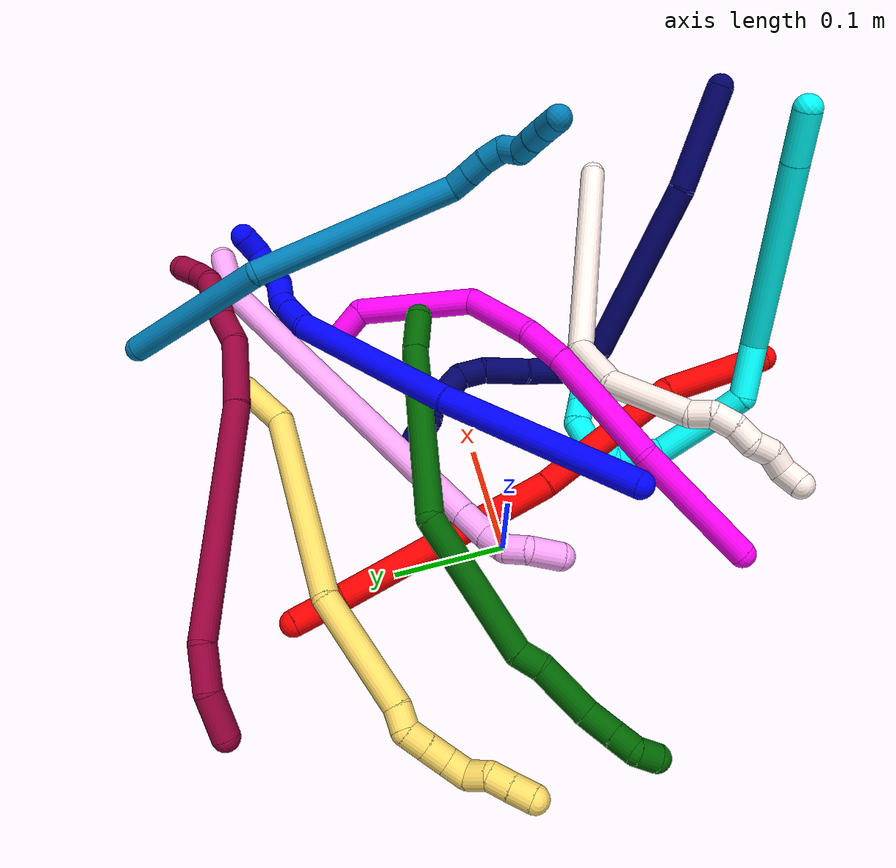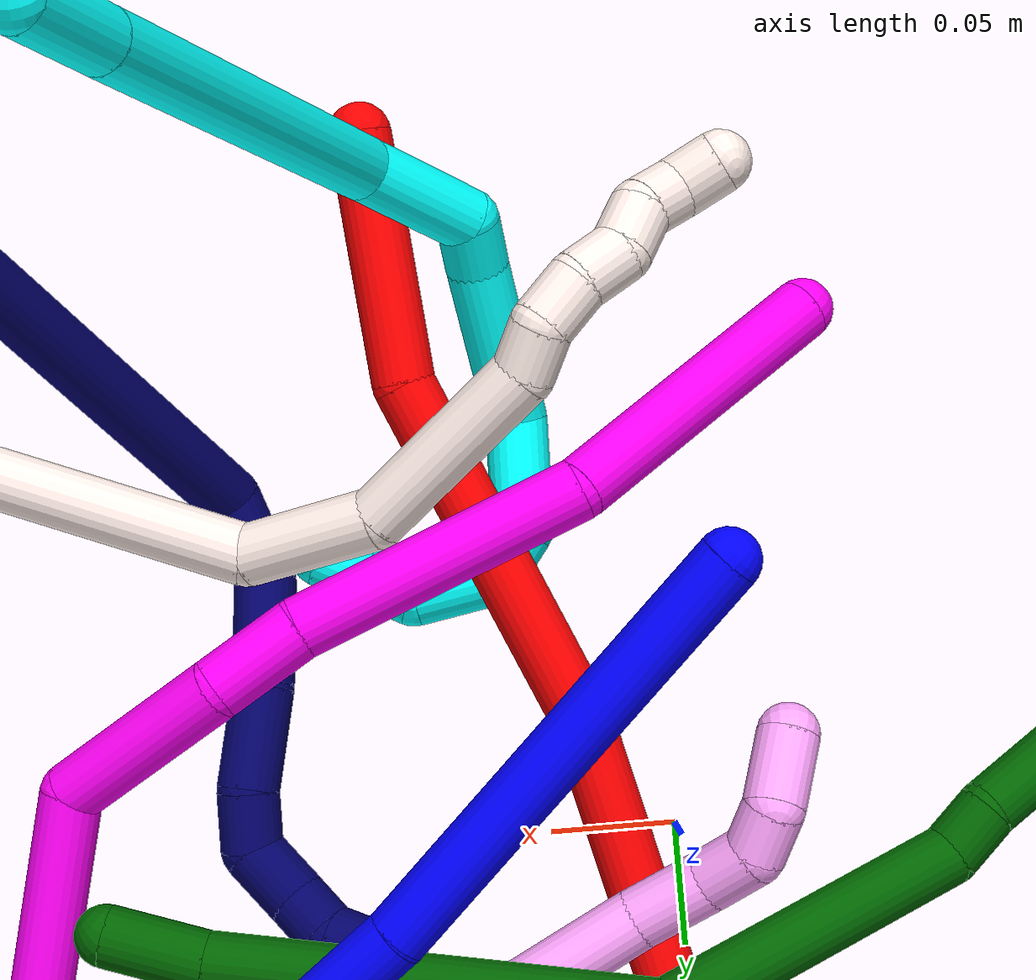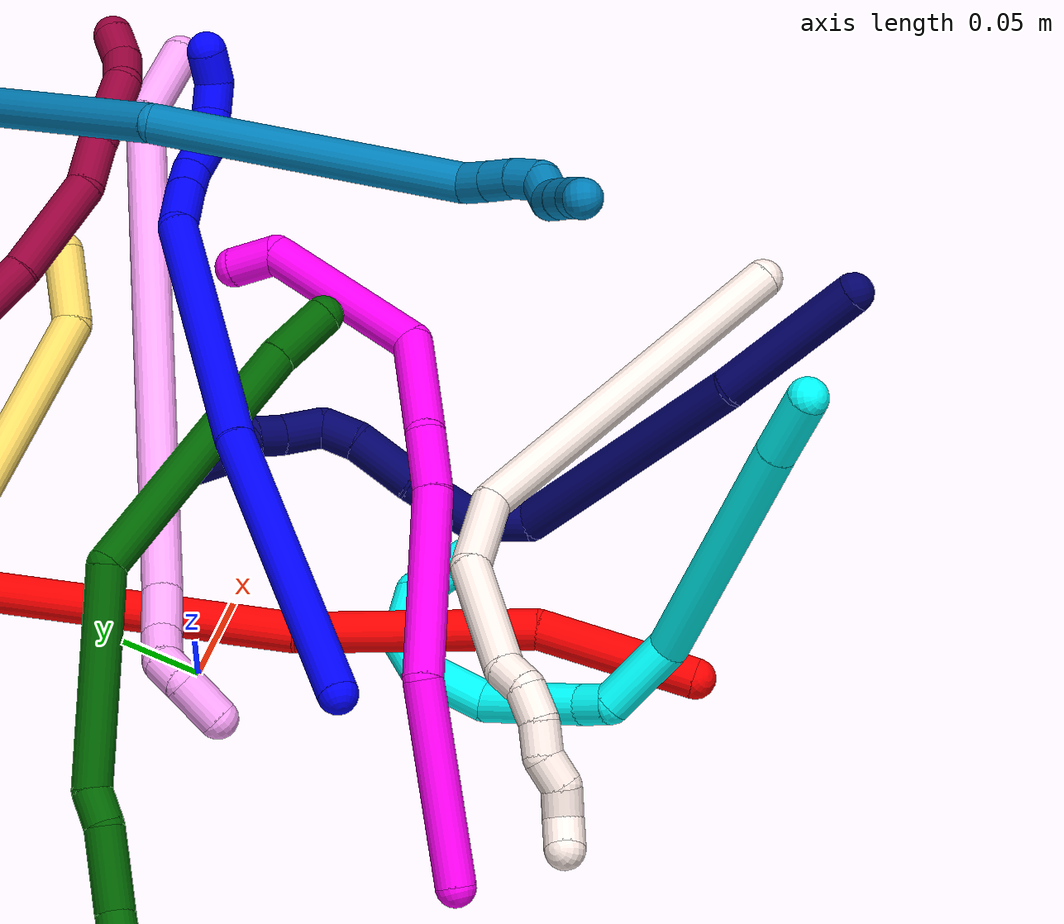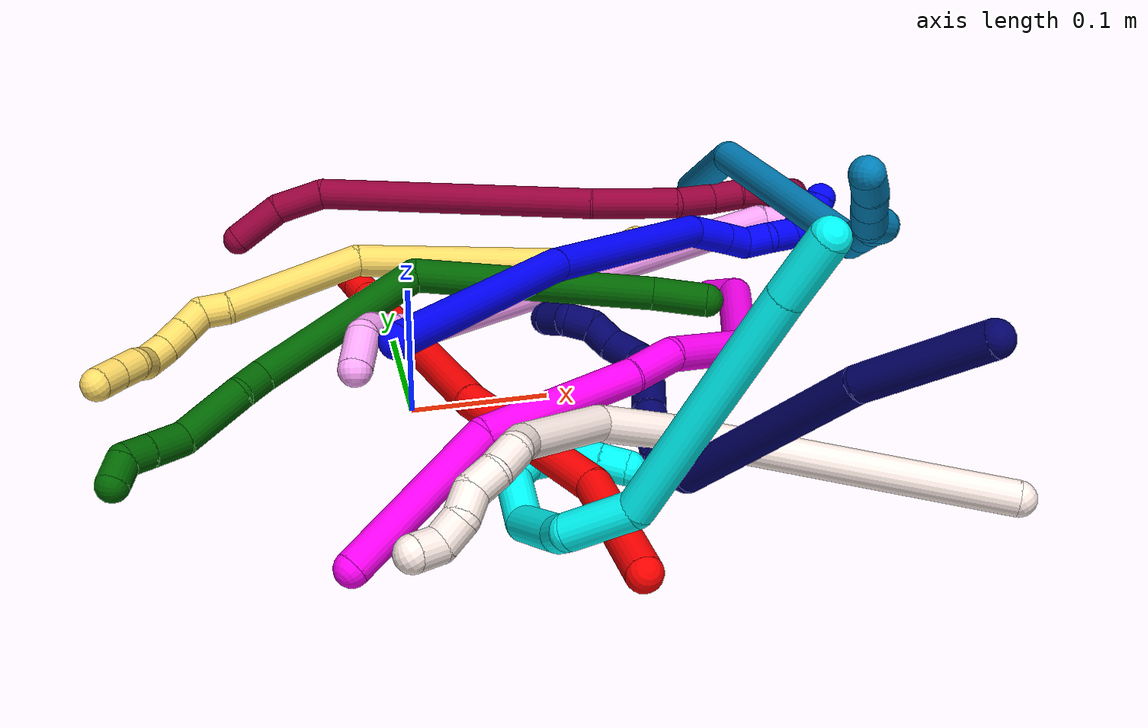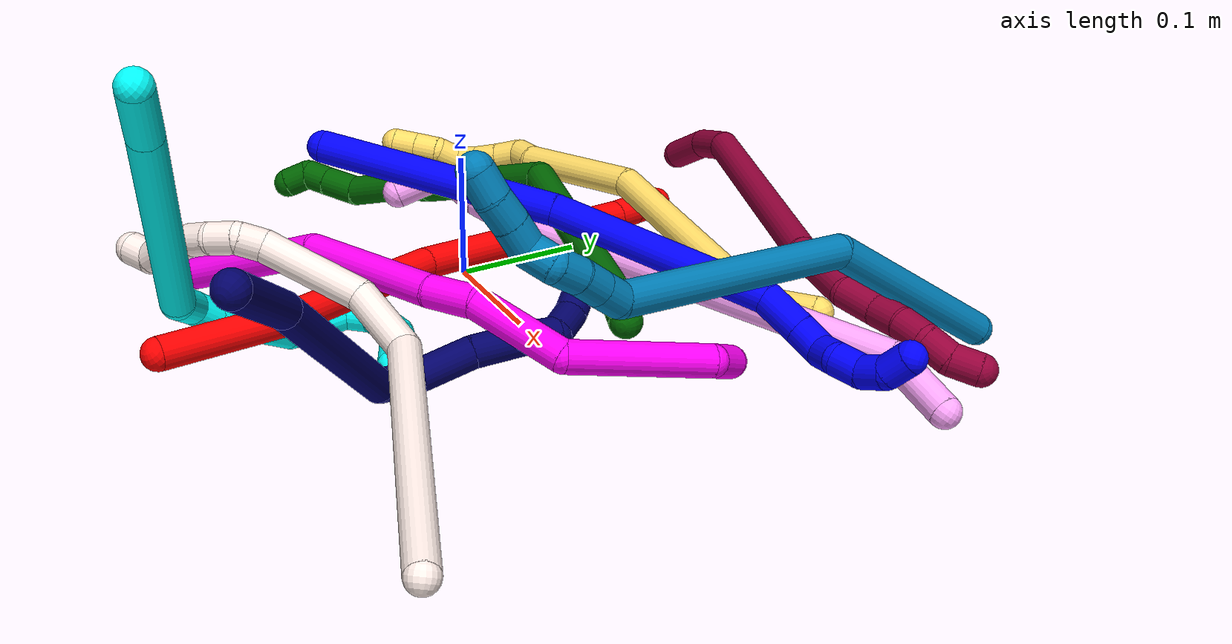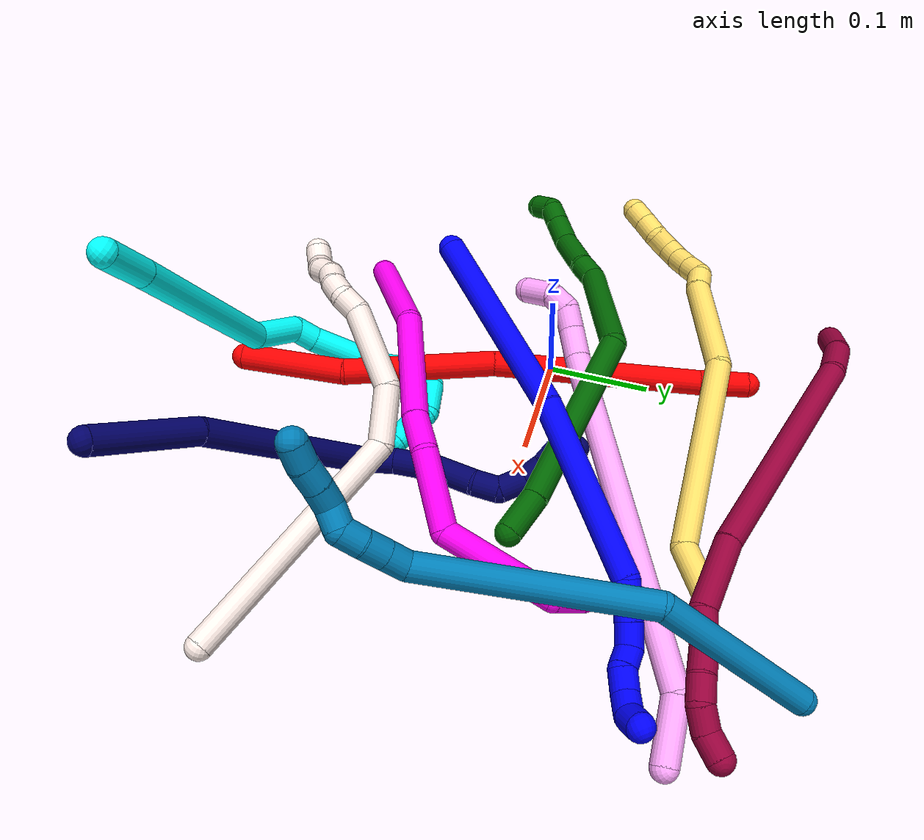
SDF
<sdf version="1.7">
 <world name="default">
  <plugin name="TubeGeneratorPlugin" filename="libtube_generator_plugin.so"/>
  <model name="photoneo_s_sensor">
   <static>1</static>
   <pose>0 0 2 1.57079 1.57079 3.14159</pose>
   <link name="link">
    <inertial><mass>0.1</mass></inertial>
    <sensor name="sensor" type="depth">
     <update_rate>30</update_rate>
     <camera>
      <horizontal_fov>1.22</horizontal_fov>
      <image><width>1920</width><height>1200</height><format>B8G8R8</format></image>
      <clip><near>0.1</near><far>4</far></clip>
      <depth_camera><output>points</output></depth_camera>
     </camera>
     <plugin name="camera_plugin" filename="libgazebo_ros_depth_camera.so">
      <baseline>0.2</baseline>
      <alwaysOn>1</alwaysOn>
      <updateRate>0.0</updateRate>
      <cameraName>camera_ir</cameraName>
      <imageTopicName>/camera/color/image_raw</imageTopicName>
      <cameraInfoTopicName>/camera/color/camera_info</cameraInfoTopicName>
      <depthImageTopicName>/camera/depth/image_raw</depthImageTopicName>
      <depthImageCameraInfoTopicName>/camera/depth/camera_info</depthImageCameraInfoTopicName>
      <pointCloudTopicName>/camera/depth/points</pointCloudTopicName>
      <frameName>fr_optical</frameName>
      <pointCloudCutoff>0.1</pointCloudCutoff>
      <pointCloudCutoffMax>2.0</pointCloudCutoffMax>
      <distortionK1>0</distortionK1>
      <distortionK2>0</distortionK2>
      <distortionK3>0</distortionK3>
      <distortionT1>0</distortionT1>
      <distortionT2>0</distortionT2>
      <CxPrime>0</CxPrime>
      <Cx>0</Cx>
      <Cy>0</Cy>
      <focalLength>0</focalLength>
      <hackBaseline>0</hackBaseline>
     </plugin>
    </sensor>
   </link>
  </model>
  <gravity>0 0 -9.8</gravity>
  <magnetic_field>6e-06 2.3e-05 -4.2e-05</magnetic_field>
  <atmosphere type="adiabatic"/>
  <physics name="default_physics" default="0" type="ode">
   <max_step_size>0.003</max_step_size>
   <real_time_factor>1</real_time_factor>
   <real_time_update_rate>1000</real_time_update_rate>
   <max_contacts>10000</max_contacts>
   <ode>
    <solver>
     <type>quick</type>
     <iters>100</iters>
     <sor>1.3</sor>
     <use_dynamic_moi_rescaling>0</use_dynamic_moi_rescaling>
    </solver>
    <constraints>
     <contact_max_correcting_vel>0</contact_max_correcting_vel>
     <contact_surface_layer>0.001</contact_surface_layer>
     <cfm>0</cfm>
     <erp>0.2</erp>
    </constraints>
   </ode>
  </physics>
  <scene><ambient>0.4 0.4 0.4 1</ambient><background>0.7 0.7 0.7 1</background><shadows>0</shadows></scene>
  <audio><device>default</device></audio>
  <spherical_coordinates>
   <surface_model>EARTH_WGS84</surface_model>
   <latitude_deg>0</latitude_deg>
   <longitude_deg>0</longitude_deg>
   <elevation>0</elevation>
   <heading_deg>0</heading_deg>
  </spherical_coordinates>
  <model name="bin">
   <static>1</static>
   <link name="bottom">
    <collision name="collision-bottom">
     <pose>0 0 -0.01 0 -0 0</pose>
     <geometry><box><size>0.8 0.6 0.02</size></box></geometry>
     <surface>
      <friction><ode><mu>100</mu><mu2>100</mu2></ode></friction>
      <contact><collide_bitmask>65535</collide_bitmask></contact>
     </surface>
    </collision>
   </link>
   <link name="west_wall">
    <collision name="collision-west_wall">
     <pose>-0.41 0 0.1 0 -0 0</pose>
     <geometry><box><size>0.02 0.6 0.2</size></box></geometry>
     <surface>
      <friction><ode><mu>100</mu><mu2>100</mu2></ode></friction>
      <contact><collide_bitmask>65535</collide_bitmask></contact>
     </surface>
    </collision>
   </link>
   <link name="east_wall">
    <collision name="collision-east_wall">
     <pose>0.41 0 0.1 0 -0 0</pose>
     <geometry><box><size>0.02 0.6 0.2</size></box></geometry>
     <surface>
      <friction><ode><mu>100</mu><mu2>100</mu2></ode></friction>
      <contact><collide_bitmask>65535</collide_bitmask></contact>
     </surface>
    </collision>
   </link>
   <link name="south_wall">
    <collision name="collision-south_wall">
     <pose>0 -0.31 0.1 0 -0 0</pose>
     <geometry><box><size>0.8 0.02 0.2</size></box></geometry>
     <surface>
      <friction><ode><mu>100</mu><mu2>100</mu2></ode></friction>
      <contact><collide_bitmask>65535</collide_bitmask></contact>
     </surface>
    </collision>
   </link>
   <link name="north_wall">
    <collision name="collision-north_wall">
     <pose>0 0.31 0.1 0 -0 0</pose>
     <geometry><box><size>0.8 0.02 0.2</size></box></geometry>
     <surface>
      <friction><ode><mu>100</mu><mu2>100</mu2></ode></friction>
      <contact><collide_bitmask>65535</collide_bitmask></contact>
     </surface>
    </collision>
   </link>
  </model>
  <model name="1">
   <static>0</static>
   <link name="1">
    <collision name="collision-cylinder-e_1_1_4">
     <pose>0.009027 0.007822 0.093321 -0.083618 0.096097 -0.004023</pose>
     <geometry><cylinder><radius>0.0125</radius><length>0.188164</length></cylinder></geometry>
     <surface>
      <friction><ode><mu>1.16</mu><mu2>1.16</mu2><slip1>0</slip1><slip2>0</slip2></ode></friction>
      <contact><ode><kp>1e+06</kp><kd>1</kd><max_vel>0</max_vel><min_depth>0.001</min_depth></ode></contact>
     </surface>
    </collision>
    <visual name="visual-cylinder-e_1_1_4">
     <pose>0.009027 0.007822 0.093321 -0.083618 0.096097 -0.004023</pose>
     <geometry><cylinder><radius>0.0125</radius><length>0.188164</length></cylinder></geometry>
     <material><ambient>0 0 1 1</ambient></material>
    </visual>
    <collision name="collision-cylinder-e_2_4_5">
     <pose>0.025144 0.01138 0.271873 0.049971 0.082891 0.002073</pose>
     <geometry><cylinder><radius>0.0125</radius><length>0.171264</length></cylinder></geometry>
     <surface>
      <friction><ode><mu>1.16</mu><mu2>1.16</mu2><slip1>0</slip1><slip2>0</slip2></ode></friction>
      <contact><ode><kp>1e+06</kp><kd>1</kd><max_vel>0</max_vel><min_depth>0.001</min_depth></ode></contact>
     </surface>
    </collision>
    <visual name="visual-cylinder-e_2_4_5">
     <pose>0.025144 0.01138 0.271873 0.049971 0.082891 0.002073</pose>
     <geometry><cylinder><radius>0.0125</radius><length>0.171264</length></cylinder></geometry>
     <material><ambient>0 0 1 1</ambient></material>
    </visual>
    <collision name="collision-cylinder-e_3_5_6">
     <pose>0.032739 -2.8e-05 0.372824 0.426672 0.0292 0.006326</pose>
     <geometry><cylinder><radius>0.0125</radius><length>0.034551</length></cylinder></geometry>
     <surface>
      <friction><ode><mu>1.16</mu><mu2>1.16</mu2><slip1>0</slip1><slip2>0</slip2></ode></friction>
      <contact><ode><kp>1e+06</kp><kd>1</kd><max_vel>0</max_vel><min_depth>0.001</min_depth></ode></contact>
     </surface>
    </collision>
    <visual name="visual-cylinder-e_3_5_6">
     <pose>0.032739 -2.8e-05 0.372824 0.426672 0.0292 0.006326</pose>
     <geometry><cylinder><radius>0.0125</radius><length>0.034551</length></cylinder></geometry>
     <material><ambient>0 0 1 1</ambient></material>
    </visual>
    <collision name="collision-cylinder-e_4_6_7">
     <pose>0.033349 -0.012358 0.398567 0.477232 0.009438 0.002296</pose>
     <geometry><cylinder><radius>0.0125</radius><length>0.022568</length></cylinder></geometry>
     <surface>
      <friction><ode><mu>1.16</mu><mu2>1.16</mu2><slip1>0</slip1><slip2>0</slip2></ode></friction>
      <contact><ode><kp>1e+06</kp><kd>1</kd><max_vel>0</max_vel><min_depth>0.001</min_depth></ode></contact>
     </surface>
    </collision>
    <visual name="visual-cylinder-e_4_6_7">
     <pose>0.033349 -0.012358 0.398567 0.477232 0.009438 0.002296</pose>
     <geometry><cylinder><radius>0.0125</radius><length>0.022568</length></cylinder></geometry>
     <material><ambient>0 0 1 1</ambient></material>
    </visual>
    <collision name="collision-cylinder-e_5_7_8">
     <pose>0.026817 -0.02065 0.415784 0.407964 -0.702739 -0.151372</pose>
     <geometry><cylinder><radius>0.0125</radius><length>0.020543</length></cylinder></geometry>
     <surface>
      <friction><ode><mu>1.16</mu><mu2>1.16</mu2><slip1>0</slip1><slip2>0</slip2></ode></friction>
      <contact><ode><kp>1e+06</kp><kd>1</kd><max_vel>0</max_vel><min_depth>0.001</min_depth></ode></contact>
     </surface>
    </collision>
    <visual name="visual-cylinder-e_5_7_8">
     <pose>0.026817 -0.02065 0.415784 0.407964 -0.702739 -0.151372</pose>
     <geometry><cylinder><radius>0.0125</radius><length>0.020543</length></cylinder></geometry>
     <material><ambient>0 0 1 1</ambient></material>
    </visual>
    <collision name="collision-cylinder-e_6_8_9">
     <pose>0.017865 -0.026005 0.433398 0.212229 -0.213796 -0.022858</pose>
     <geometry><cylinder><radius>0.0125</radius><length>0.021813</length></cylinder></geometry>
     <surface>
      <friction><ode><mu>1.16</mu><mu2>1.16</mu2><slip1>0</slip1><slip2>0</slip2></ode></friction>
      <contact><ode><kp>1e+06</kp><kd>1</kd><max_vel>0</max_vel><min_depth>0.001</min_depth></ode></contact>
     </surface>
    </collision>
    <visual name="visual-cylinder-e_6_8_9">
     <pose>0.017865 -0.026005 0.433398 0.212229 -0.213796 -0.022858</pose>
     <geometry><cylinder><radius>0.0125</radius><length>0.021813</length></cylinder></geometry>
     <material><ambient>0 0 1 1</ambient></material>
    </visual>
    <collision name="collision-cylinder-e_7_9_10">
     <pose>0.010149 -0.027409 0.452307 -0.098649 -0.56447 0.028627</pose>
     <geometry><cylinder><radius>0.0125</radius><length>0.020196</length></cylinder></geometry>
     <surface>
      <friction><ode><mu>1.16</mu><mu2>1.16</mu2><slip1>0</slip1><slip2>0</slip2></ode></friction>
      <contact><ode><kp>1e+06</kp><kd>1</kd><max_vel>0</max_vel><min_depth>0.001</min_depth></ode></contact>
     </surface>
    </collision>
    <visual name="visual-cylinder-e_7_9_10">
     <pose>0.010149 -0.027409 0.452307 -0.098649 -0.56447 0.028627</pose>
     <geometry><cylinder><radius>0.0125</radius><length>0.020196</length></cylinder></geometry>
     <material><ambient>0 0 1 1</ambient></material>
    </visual>
    <collision name="collision-cylinder-e_8_10_2">
     <pose>-0.000929 -0.020665 0.467289 -0.738096 -0.574095 0.227364</pose>
     <geometry><cylinder><radius>0.0125</radius><length>0.020901</length></cylinder></geometry>
     <surface>
      <friction><ode><mu>1.16</mu><mu2>1.16</mu2><slip1>0</slip1><slip2>0</slip2></ode></friction>
      <contact><ode><kp>1e+06</kp><kd>1</kd><max_vel>0</max_vel><min_depth>0.001</min_depth></ode></contact>
     </surface>
    </collision>
    <visual name="visual-cylinder-e_8_10_2">
     <pose>-0.000929 -0.020665 0.467289 -0.738096 -0.574095 0.227364</pose>
     <geometry><cylinder><radius>0.0125</radius><length>0.020901</length></cylinder></geometry>
     <material><ambient>0 0 1 1</ambient></material>
    </visual>
    <collision name="collision-sphere-2">
     <pose>-0.006604 -0.01476 0.47378 0 -0 0</pose>
     <geometry><sphere><radius>0.0125</radius></sphere></geometry>
     <surface>
      <friction><ode><mu>1.16</mu><mu2>1.16</mu2><slip1>0</slip1><slip2>0</slip2></ode></friction>
      <contact><ode><kp>1e+06</kp><kd>1</kd><max_vel>0</max_vel><min_depth>0.001</min_depth></ode></contact>
     </surface>
    </collision>
    <visual name="visual-sphere-2">
     <pose>-0.006604 -0.01476 0.47378 0 -0 0</pose>
     <geometry><sphere><radius>0.0125</radius></sphere></geometry>
     <material><ambient>0 0 1 1</ambient></material>
    </visual>
    <collision name="collision-sphere-10">
     <pose>0.004746 -0.026569 0.460797 0 -0 0</pose>
     <geometry><sphere><radius>0.0125</radius></sphere></geometry>
     <surface>
      <friction><ode><mu>1.16</mu><mu2>1.16</mu2><slip1>0</slip1><slip2>0</slip2></ode></friction>
      <contact><ode><kp>1e+06</kp><kd>1</kd><max_vel>0</max_vel><min_depth>0.001</min_depth></ode></contact>
     </surface>
    </collision>
    <visual name="visual-sphere-10">
     <pose>0.004746 -0.026569 0.460797 0 -0 0</pose>
     <geometry><sphere><radius>0.0125</radius></sphere></geometry>
     <material><ambient>0 0 1 1</ambient></material>
    </visual>
    <collision name="collision-sphere-9">
     <pose>0.015551 -0.02825 0.443817 0 -0 0</pose>
     <geometry><sphere><radius>0.0125</radius></sphere></geometry>
     <surface>
      <friction><ode><mu>1.16</mu><mu2>1.16</mu2><slip1>0</slip1><slip2>0</slip2></ode></friction>
      <contact><ode><kp>1e+06</kp><kd>1</kd><max_vel>0</max_vel><min_depth>0.001</min_depth></ode></contact>
     </surface>
    </collision>
    <visual name="visual-sphere-9">
     <pose>0.015551 -0.02825 0.443817 0 -0 0</pose>
     <geometry><sphere><radius>0.0125</radius></sphere></geometry>
     <material><ambient>0 0 1 1</ambient></material>
    </visual>
    <collision name="collision-sphere-4">
     <pose>0.018054 0.015643 0.186642 0 -0 0</pose>
     <geometry><sphere><radius>0.0125</radius></sphere></geometry>
     <surface>
      <friction><ode><mu>1.16</mu><mu2>1.16</mu2><slip1>0</slip1><slip2>0</slip2></ode></friction>
      <contact><ode><kp>1e+06</kp><kd>1</kd><max_vel>0</max_vel><min_depth>0.001</min_depth></ode></contact>
     </surface>
    </collision>
    <visual name="visual-sphere-4">
     <pose>0.018054 0.015643 0.186642 0 -0 0</pose>
     <geometry><sphere><radius>0.0125</radius></sphere></geometry>
     <material><ambient>0 0 1 1</ambient></material>
    </visual>
    <collision name="collision-sphere-1">
     <geometry><sphere><radius>0.0125</radius></sphere></geometry>
     <surface>
      <friction><ode><mu>1.16</mu><mu2>1.16</mu2><slip1>0</slip1><slip2>0</slip2></ode></friction>
      <contact><ode><kp>1e+06</kp><kd>1</kd><max_vel>0</max_vel><min_depth>0.001</min_depth></ode></contact>
     </surface>
    </collision>
    <visual name="visual-sphere-1">
     <geometry><sphere><radius>0.0125</radius></sphere></geometry>
     <material><ambient>0 0 1 1</ambient></material>
    </visual>
    <collision name="collision-sphere-8">
     <pose>0.020179 -0.02376 0.422979 0 -0 0</pose>
     <geometry><sphere><radius>0.0125</radius></sphere></geometry>
     <surface>
      <friction><ode><mu>1.16</mu><mu2>1.16</mu2><slip1>0</slip1><slip2>0</slip2></ode></friction>
      <contact><ode><kp>1e+06</kp><kd>1</kd><max_vel>0</max_vel><min_depth>0.001</min_depth></ode></contact>
     </surface>
    </collision>
    <visual name="visual-sphere-8">
     <pose>0.020179 -0.02376 0.422979 0 -0 0</pose>
     <geometry><sphere><radius>0.0125</radius></sphere></geometry>
     <material><ambient>0 0 1 1</ambient></material>
    </visual>
    <collision name="collision-sphere-5">
     <pose>0.032234 0.007118 0.357104 0 -0 0</pose>
     <geometry><sphere><radius>0.0125</radius></sphere></geometry>
     <surface>
      <friction><ode><mu>1.16</mu><mu2>1.16</mu2><slip1>0</slip1><slip2>0</slip2></ode></friction>
      <contact><ode><kp>1e+06</kp><kd>1</kd><max_vel>0</max_vel><min_depth>0.001</min_depth></ode></contact>
     </surface>
    </collision>
    <visual name="visual-sphere-5">
     <pose>0.032234 0.007118 0.357104 0 -0 0</pose>
     <geometry><sphere><radius>0.0125</radius></sphere></geometry>
     <material><ambient>0 0 1 1</ambient></material>
    </visual>
    <collision name="collision-sphere-6">
     <pose>0.033243 -0.007175 0.388544 0 -0 0</pose>
     <geometry><sphere><radius>0.0125</radius></sphere></geometry>
     <surface>
      <friction><ode><mu>1.16</mu><mu2>1.16</mu2><slip1>0</slip1><slip2>0</slip2></ode></friction>
      <contact><ode><kp>1e+06</kp><kd>1</kd><max_vel>0</max_vel><min_depth>0.001</min_depth></ode></contact>
     </surface>
    </collision>
    <visual name="visual-sphere-6">
     <pose>0.033243 -0.007175 0.388544 0 -0 0</pose>
     <geometry><sphere><radius>0.0125</radius></sphere></geometry>
     <material><ambient>0 0 1 1</ambient></material>
    </visual>
    <collision name="collision-sphere-7">
     <pose>0.033456 -0.01754 0.40859 0 -0 0</pose>
     <geometry><sphere><radius>0.0125</radius></sphere></geometry>
     <surface>
      <friction><ode><mu>1.16</mu><mu2>1.16</mu2><slip1>0</slip1><slip2>0</slip2></ode></friction>
      <contact><ode><kp>1e+06</kp><kd>1</kd><max_vel>0</max_vel><min_depth>0.001</min_depth></ode></contact>
     </surface>
    </collision>
    <visual name="visual-sphere-7">
     <pose>0.033456 -0.01754 0.40859 0 -0 0</pose>
     <geometry><sphere><radius>0.0125</radius></sphere></geometry>
     <material><ambient>0 0 1 1</ambient></material>
    </visual>
    <inertial>
     <pose>0.01803 0.002328 0.245789 0 -0 0</pose>
     <mass>0.5</mass>
     <inertia>
      <ixx>0.000994</ixx>
      <ixy>0</ixy>
      <ixz>0</ixz>
      <iyy>0.000995</iyy>
      <iyz>0</iyz>
      <izz>-7.2e-05</izz>
     </inertia>
    </inertial>
   </link>
   <pose>-0.021336 -0.105927 0.123549 1.77062 0.829461 2.36517</pose>
  </model>
  <model name="2">
   <static>0</static>
   <link name="2">
    <collision name="collision-cylinder-e_1_1_4">
     <pose>-0.002732 0.038955 -0.030456 -2.23435 -0.055198 0.113127</pose>
     <geometry><cylinder><radius>0.0125</radius><length>0.099046</length></cylinder></geometry>
     <surface>
      <friction><ode><mu>1.16</mu><mu2>1.16</mu2><slip1>0</slip1><slip2>0</slip2></ode></friction>
      <contact><ode><kp>1e+06</kp><kd>1</kd><max_vel>0</max_vel><min_depth>0.001</min_depth></ode></contact>
     </surface>
    </collision>
    <visual name="visual-cylinder-e_1_1_4">
     <pose>-0.002732 0.038955 -0.030456 -2.23435 -0.055198 0.113127</pose>
     <geometry><cylinder><radius>0.0125</radius><length>0.099046</length></cylinder></geometry>
     <material><ambient>1 0 0 1</ambient></material>
    </visual>
    <collision name="collision-cylinder-e_2_4_5">
     <pose>-0.031253 0.127071 -0.108557 -2.34055 -0.36025 0.812326</pose>
     <geometry><cylinder><radius>0.0125</radius><length>0.146314</length></cylinder></geometry>
     <surface>
      <friction><ode><mu>1.16</mu><mu2>1.16</mu2><slip1>0</slip1><slip2>0</slip2></ode></friction>
      <contact><ode><kp>1e+06</kp><kd>1</kd><max_vel>0</max_vel><min_depth>0.001</min_depth></ode></contact>
     </surface>
    </collision>
    <visual name="visual-cylinder-e_2_4_5">
     <pose>-0.031253 0.127071 -0.108557 -2.34055 -0.36025 0.812326</pose>
     <geometry><cylinder><radius>0.0125</radius><length>0.146314</length></cylinder></geometry>
     <material><ambient>1 0 0 1</ambient></material>
    </visual>
    <collision name="collision-cylinder-e_3_5_6">
     <pose>-0.0764 0.248715 -0.22676 -2.34273 -0.18909 0.441955</pose>
     <geometry><cylinder><radius>0.0125</radius><length>0.20598</length></cylinder></geometry>
     <surface>
      <friction><ode><mu>1.16</mu><mu2>1.16</mu2><slip1>0</slip1><slip2>0</slip2></ode></friction>
      <contact><ode><kp>1e+06</kp><kd>1</kd><max_vel>0</max_vel><min_depth>0.001</min_depth></ode></contact>
     </surface>
    </collision>
    <visual name="visual-cylinder-e_3_5_6">
     <pose>-0.0764 0.248715 -0.22676 -2.34273 -0.18909 0.441955</pose>
     <geometry><cylinder><radius>0.0125</radius><length>0.20598</length></cylinder></geometry>
     <material><ambient>1 0 0 1</ambient></material>
    </visual>
    <collision name="collision-cylinder-e_4_6_7">
     <pose>-0.097776 0.328893 -0.304026 -2.28776 -0.195121 0.423843</pose>
     <geometry><cylinder><radius>0.0125</radius><length>0.02081</length></cylinder></geometry>
     <surface>
      <friction><ode><mu>1.16</mu><mu2>1.16</mu2><slip1>0</slip1><slip2>0</slip2></ode></friction>
      <contact><ode><kp>1e+06</kp><kd>1</kd><max_vel>0</max_vel><min_depth>0.001</min_depth></ode></contact>
     </surface>
    </collision>
    <visual name="visual-cylinder-e_4_6_7">
     <pose>-0.097776 0.328893 -0.304026 -2.28776 -0.195121 0.423843</pose>
     <geometry><cylinder><radius>0.0125</radius><length>0.02081</length></cylinder></geometry>
     <material><ambient>1 0 0 1</ambient></material>
    </visual>
    <collision name="collision-cylinder-e_5_7_2">
     <pose>-0.102681 0.347061 -0.319443 -2.26449 -0.208902 0.439805</pose>
     <geometry><cylinder><radius>0.0125</radius><length>0.02785</length></cylinder></geometry>
     <surface>
      <friction><ode><mu>1.16</mu><mu2>1.16</mu2><slip1>0</slip1><slip2>0</slip2></ode></friction>
      <contact><ode><kp>1e+06</kp><kd>1</kd><max_vel>0</max_vel><min_depth>0.001</min_depth></ode></contact>
     </surface>
    </collision>
    <visual name="visual-cylinder-e_5_7_2">
     <pose>-0.102681 0.347061 -0.319443 -2.26449 -0.208902 0.439805</pose>
     <geometry><cylinder><radius>0.0125</radius><length>0.02785</length></cylinder></geometry>
     <material><ambient>1 0 0 1</ambient></material>
    </visual>
    <collision name="collision-sphere-2">
     <pose>-0.105569 0.357535 -0.328153 0 -0 0</pose>
     <geometry><sphere><radius>0.0125</radius></sphere></geometry>
     <surface>
      <friction><ode><mu>1.16</mu><mu2>1.16</mu2><slip1>0</slip1><slip2>0</slip2></ode></friction>
      <contact><ode><kp>1e+06</kp><kd>1</kd><max_vel>0</max_vel><min_depth>0.001</min_depth></ode></contact>
     </surface>
    </collision>
    <visual name="visual-sphere-2">
     <pose>-0.105569 0.357535 -0.328153 0 -0 0</pose>
     <geometry><sphere><radius>0.0125</radius></sphere></geometry>
     <material><ambient>1 0 0 1</ambient></material>
    </visual>
    <collision name="collision-sphere-7">
     <pose>-0.099793 0.336587 -0.310733 0 -0 0</pose>
     <geometry><sphere><radius>0.0125</radius></sphere></geometry>
     <surface>
      <friction><ode><mu>1.16</mu><mu2>1.16</mu2><slip1>0</slip1><slip2>0</slip2></ode></friction>
      <contact><ode><kp>1e+06</kp><kd>1</kd><max_vel>0</max_vel><min_depth>0.001</min_depth></ode></contact>
     </surface>
    </collision>
    <visual name="visual-sphere-7">
     <pose>-0.099793 0.336587 -0.310733 0 -0 0</pose>
     <geometry><sphere><radius>0.0125</radius></sphere></geometry>
     <material><ambient>1 0 0 1</ambient></material>
    </visual>
    <collision name="collision-sphere-6">
     <pose>-0.095758 0.321198 -0.297318 0 -0 0</pose>
     <geometry><sphere><radius>0.0125</radius></sphere></geometry>
     <surface>
      <friction><ode><mu>1.16</mu><mu2>1.16</mu2><slip1>0</slip1><slip2>0</slip2></ode></friction>
      <contact><ode><kp>1e+06</kp><kd>1</kd><max_vel>0</max_vel><min_depth>0.001</min_depth></ode></contact>
     </surface>
    </collision>
    <visual name="visual-sphere-6">
     <pose>-0.095758 0.321198 -0.297318 0 -0 0</pose>
     <geometry><sphere><radius>0.0125</radius></sphere></geometry>
     <material><ambient>1 0 0 1</ambient></material>
    </visual>
    <collision name="collision-sphere-5">
     <pose>-0.057041 0.176232 -0.156203 0 -0 0</pose>
     <geometry><sphere><radius>0.0125</radius></sphere></geometry>
     <surface>
      <friction><ode><mu>1.16</mu><mu2>1.16</mu2><slip1>0</slip1><slip2>0</slip2></ode></friction>
      <contact><ode><kp>1e+06</kp><kd>1</kd><max_vel>0</max_vel><min_depth>0.001</min_depth></ode></contact>
     </surface>
    </collision>
    <visual name="visual-sphere-5">
     <pose>-0.057041 0.176232 -0.156203 0 -0 0</pose>
     <geometry><sphere><radius>0.0125</radius></sphere></geometry>
     <material><ambient>1 0 0 1</ambient></material>
    </visual>
    <collision name="collision-sphere-1">
     <geometry><sphere><radius>0.0125</radius></sphere></geometry>
     <surface>
      <friction><ode><mu>1.16</mu><mu2>1.16</mu2><slip1>0</slip1><slip2>0</slip2></ode></friction>
      <contact><ode><kp>1e+06</kp><kd>1</kd><max_vel>0</max_vel><min_depth>0.001</min_depth></ode></contact>
     </surface>
    </collision>
    <visual name="visual-sphere-1">
     <geometry><sphere><radius>0.0125</radius></sphere></geometry>
     <material><ambient>1 0 0 1</ambient></material>
    </visual>
    <collision name="collision-sphere-4">
     <pose>-0.005464 0.077911 -0.060911 0 -0 0</pose>
     <geometry><sphere><radius>0.0125</radius></sphere></geometry>
     <surface>
      <friction><ode><mu>1.16</mu><mu2>1.16</mu2><slip1>0</slip1><slip2>0</slip2></ode></friction>
      <contact><ode><kp>1e+06</kp><kd>1</kd><max_vel>0</max_vel><min_depth>0.001</min_depth></ode></contact>
     </surface>
    </collision>
    <visual name="visual-sphere-4">
     <pose>-0.005464 0.077911 -0.060911 0 -0 0</pose>
     <geometry><sphere><radius>0.0125</radius></sphere></geometry>
     <material><ambient>1 0 0 1</ambient></material>
    </visual>
    <inertial>
     <pose>-0.050949 0.180382 -0.161663 0 -0 0</pose>
     <mass>0.5</mass>
     <inertia>
      <ixx>0.001407</ixx>
      <ixy>0</ixy>
      <ixz>0</ixz>
      <iyy>-2.4e-05</iyy>
      <iyz>0</iyz>
      <izz>-0.000555</izz>
     </inertia>
    </inertial>
   </link>
   <pose>0.102298 -0.282203 0.048633 0.641828 0.10795 0.034063</pose>
  </model>
  <model name="3">
   <static>0</static>
   <link name="3">
    <collision name="collision-cylinder-e_1_1_4">
     <pose>-0.00895 -0.011032 -0.017558 2.5806 -0.407468 -1.24427</pose>
     <geometry><cylinder><radius>0.0125</radius><length>0.045171</length></cylinder></geometry>
     <surface>
      <friction><ode><mu>1.16</mu><mu2>1.16</mu2><slip1>0</slip1><slip2>0</slip2></ode></friction>
      <contact><ode><kp>1e+06</kp><kd>1</kd><max_vel>0</max_vel><min_depth>0.001</min_depth></ode></contact>
     </surface>
    </collision>
    <visual name="visual-cylinder-e_1_1_4">
     <pose>-0.00895 -0.011032 -0.017558 2.5806 -0.407468 -1.24427</pose>
     <geometry><cylinder><radius>0.0125</radius><length>0.045171</length></cylinder></geometry>
     <material><ambient>0.003922 1 0.996078 1</ambient></material>
    </visual>
    <collision name="collision-cylinder-e_2_4_5">
     <pose>-0.051287 -0.066509 -0.102643 2.5595 -0.39165 -1.16982</pose>
     <geometry><cylinder><radius>0.0125</radius><length>0.174927</length></cylinder></geometry>
     <surface>
      <friction><ode><mu>1.16</mu><mu2>1.16</mu2><slip1>0</slip1><slip2>0</slip2></ode></friction>
      <contact><ode><kp>1e+06</kp><kd>1</kd><max_vel>0</max_vel><min_depth>0.001</min_depth></ode></contact>
     </surface>
    </collision>
    <visual name="visual-cylinder-e_2_4_5">
     <pose>-0.051287 -0.066509 -0.102643 2.5595 -0.39165 -1.16982</pose>
     <geometry><cylinder><radius>0.0125</radius><length>0.174927</length></cylinder></geometry>
     <material><ambient>0.003922 1 0.996078 1</ambient></material>
    </visual>
    <collision name="collision-cylinder-e_3_5_6">
     <pose>-0.102637 -0.113335 -0.187203 3.00263 -0.807204 -2.81849</pose>
     <geometry><cylinder><radius>0.0125</radius><length>0.04974</length></cylinder></geometry>
     <surface>
      <friction><ode><mu>1.16</mu><mu2>1.16</mu2><slip1>0</slip1><slip2>0</slip2></ode></friction>
      <contact><ode><kp>1e+06</kp><kd>1</kd><max_vel>0</max_vel><min_depth>0.001</min_depth></ode></contact>
     </surface>
    </collision>
    <visual name="visual-cylinder-e_3_5_6">
     <pose>-0.102637 -0.113335 -0.187203 3.00263 -0.807204 -2.81849</pose>
     <geometry><cylinder><radius>0.0125</radius><length>0.04974</length></cylinder></geometry>
     <material><ambient>0.003922 1 0.996078 1</ambient></material>
    </visual>
    <collision name="collision-cylinder-e_4_6_7">
     <pose>-0.121307 -0.114311 -0.214828 -3.00958 -0.065824 0.9242</pose>
     <geometry><cylinder><radius>0.0125</radius><length>0.021419</length></cylinder></geometry>
     <surface>
      <friction><ode><mu>1.16</mu><mu2>1.16</mu2><slip1>0</slip1><slip2>0</slip2></ode></friction>
      <contact><ode><kp>1e+06</kp><kd>1</kd><max_vel>0</max_vel><min_depth>0.001</min_depth></ode></contact>
     </surface>
    </collision>
    <visual name="visual-cylinder-e_4_6_7">
     <pose>-0.121307 -0.114311 -0.214828 -3.00958 -0.065824 0.9242</pose>
     <geometry><cylinder><radius>0.0125</radius><length>0.021419</length></cylinder></geometry>
     <material><ambient>0.003922 1 0.996078 1</ambient></material>
    </visual>
    <collision name="collision-cylinder-e_5_7_8">
     <pose>-0.126184 -0.102904 -0.258112 -2.84473 -0.121463 0.772434</pose>
     <geometry><cylinder><radius>0.0125</radius><length>0.068877</length></cylinder></geometry>
     <surface>
      <friction><ode><mu>1.16</mu><mu2>1.16</mu2><slip1>0</slip1><slip2>0</slip2></ode></friction>
      <contact><ode><kp>1e+06</kp><kd>1</kd><max_vel>0</max_vel><min_depth>0.001</min_depth></ode></contact>
     </surface>
    </collision>
    <visual name="visual-cylinder-e_5_7_8">
     <pose>-0.126184 -0.102904 -0.258112 -2.84473 -0.121463 0.772434</pose>
     <geometry><cylinder><radius>0.0125</radius><length>0.068877</length></cylinder></geometry>
     <material><ambient>0.003922 1 0.996078 1</ambient></material>
    </visual>
    <collision name="collision-cylinder-e_6_8_9">
     <pose>-0.129892 -0.074787 -0.303826 -2.19413 0.020815 -0.040596</pose>
     <geometry><cylinder><radius>0.0125</radius><length>0.044636</length></cylinder></geometry>
     <surface>
      <friction><ode><mu>1.16</mu><mu2>1.16</mu2><slip1>0</slip1><slip2>0</slip2></ode></friction>
      <contact><ode><kp>1e+06</kp><kd>1</kd><max_vel>0</max_vel><min_depth>0.001</min_depth></ode></contact>
     </surface>
    </collision>
    <visual name="visual-cylinder-e_6_8_9">
     <pose>-0.129892 -0.074787 -0.303826 -2.19413 0.020815 -0.040596</pose>
     <geometry><cylinder><radius>0.0125</radius><length>0.044636</length></cylinder></geometry>
     <material><ambient>0.003922 1 0.996078 1</ambient></material>
    </visual>
    <collision name="collision-cylinder-e_7_9_10">
     <pose>-0.122841 -0.050607 -0.322987 -2.36214 0.652185 -1.37759</pose>
     <geometry><cylinder><radius>0.0125</radius><length>0.021706</length></cylinder></geometry>
     <surface>
      <friction><ode><mu>1.16</mu><mu2>1.16</mu2><slip1>0</slip1><slip2>0</slip2></ode></friction>
      <contact><ode><kp>1e+06</kp><kd>1</kd><max_vel>0</max_vel><min_depth>0.001</min_depth></ode></contact>
     </surface>
    </collision>
    <visual name="visual-cylinder-e_7_9_10">
     <pose>-0.122841 -0.050607 -0.322987 -2.36214 0.652185 -1.37759</pose>
     <geometry><cylinder><radius>0.0125</radius><length>0.021706</length></cylinder></geometry>
     <material><ambient>0.003922 1 0.996078 1</ambient></material>
    </visual>
    <collision name="collision-cylinder-e_8_10_11">
     <pose>-0.100062 -0.042162 -0.330636 -2.13687 1.39819 -1.98402</pose>
     <geometry><cylinder><radius>0.0125</radius><length>0.032871</length></cylinder></geometry>
     <surface>
      <friction><ode><mu>1.16</mu><mu2>1.16</mu2><slip1>0</slip1><slip2>0</slip2></ode></friction>
      <contact><ode><kp>1e+06</kp><kd>1</kd><max_vel>0</max_vel><min_depth>0.001</min_depth></ode></contact>
     </surface>
    </collision>
    <visual name="visual-cylinder-e_8_10_11">
     <pose>-0.100062 -0.042162 -0.330636 -2.13687 1.39819 -1.98402</pose>
     <geometry><cylinder><radius>0.0125</radius><length>0.032871</length></cylinder></geometry>
     <material><ambient>0.003922 1 0.996078 1</ambient></material>
    </visual>
    <collision name="collision-cylinder-e_9_11_12">
     <pose>-0.07479 -0.043565 -0.329187 0.906731 1.08396 0.570711</pose>
     <geometry><cylinder><radius>0.0125</radius><length>0.02055</length></cylinder></geometry>
     <surface>
      <friction><ode><mu>1.16</mu><mu2>1.16</mu2><slip1>0</slip1><slip2>0</slip2></ode></friction>
      <contact><ode><kp>1e+06</kp><kd>1</kd><max_vel>0</max_vel><min_depth>0.001</min_depth></ode></contact>
     </surface>
    </collision>
    <visual name="visual-cylinder-e_9_11_12">
     <pose>-0.07479 -0.043565 -0.329187 0.906731 1.08396 0.570711</pose>
     <geometry><cylinder><radius>0.0125</radius><length>0.02055</length></cylinder></geometry>
     <material><ambient>0.003922 1 0.996078 1</ambient></material>
    </visual>
    <collision name="collision-cylinder-e_10_12_2">
     <pose>-0.056827 -0.051151 -0.323448 0.93993 1.08353 0.593328</pose>
     <geometry><cylinder><radius>0.0125</radius><length>0.020104</length></cylinder></geometry>
     <surface>
      <friction><ode><mu>1.16</mu><mu2>1.16</mu2><slip1>0</slip1><slip2>0</slip2></ode></friction>
      <contact><ode><kp>1e+06</kp><kd>1</kd><max_vel>0</max_vel><min_depth>0.001</min_depth></ode></contact>
     </surface>
    </collision>
    <visual name="visual-cylinder-e_10_12_2">
     <pose>-0.056827 -0.051151 -0.323448 0.93993 1.08353 0.593328</pose>
     <geometry><cylinder><radius>0.0125</radius><length>0.020104</length></cylinder></geometry>
     <material><ambient>0.003922 1 0.996078 1</ambient></material>
    </visual>
    <collision name="collision-sphere-2">
     <pose>-0.047945 -0.054952 -0.320672 0 -0 0</pose>
     <geometry><sphere><radius>0.0125</radius></sphere></geometry>
     <surface>
      <friction><ode><mu>1.16</mu><mu2>1.16</mu2><slip1>0</slip1><slip2>0</slip2></ode></friction>
      <contact><ode><kp>1e+06</kp><kd>1</kd><max_vel>0</max_vel><min_depth>0.001</min_depth></ode></contact>
     </surface>
    </collision>
    <visual name="visual-sphere-2">
     <pose>-0.047945 -0.054952 -0.320672 0 -0 0</pose>
     <geometry><sphere><radius>0.0125</radius></sphere></geometry>
     <material><ambient>0.003922 1 0.996078 1</ambient></material>
    </visual>
    <collision name="collision-sphere-12">
     <pose>-0.065709 -0.047351 -0.326224 0 -0 0</pose>
     <geometry><sphere><radius>0.0125</radius></sphere></geometry>
     <surface>
      <friction><ode><mu>1.16</mu><mu2>1.16</mu2><slip1>0</slip1><slip2>0</slip2></ode></friction>
      <contact><ode><kp>1e+06</kp><kd>1</kd><max_vel>0</max_vel><min_depth>0.001</min_depth></ode></contact>
     </surface>
    </collision>
    <visual name="visual-sphere-12">
     <pose>-0.065709 -0.047351 -0.326224 0 -0 0</pose>
     <geometry><sphere><radius>0.0125</radius></sphere></geometry>
     <material><ambient>0.003922 1 0.996078 1</ambient></material>
    </visual>
    <collision name="collision-sphere-11">
     <pose>-0.083871 -0.03978 -0.33215 0 -0 0</pose>
     <geometry><sphere><radius>0.0125</radius></sphere></geometry>
     <surface>
      <friction><ode><mu>1.16</mu><mu2>1.16</mu2><slip1>0</slip1><slip2>0</slip2></ode></friction>
      <contact><ode><kp>1e+06</kp><kd>1</kd><max_vel>0</max_vel><min_depth>0.001</min_depth></ode></contact>
     </surface>
    </collision>
    <visual name="visual-sphere-11">
     <pose>-0.083871 -0.03978 -0.33215 0 -0 0</pose>
     <geometry><sphere><radius>0.0125</radius></sphere></geometry>
     <material><ambient>0.003922 1 0.996078 1</ambient></material>
    </visual>
    <collision name="collision-sphere-10">
     <pose>-0.116254 -0.044545 -0.329122 0 -0 0</pose>
     <geometry><sphere><radius>0.0125</radius></sphere></geometry>
     <surface>
      <friction><ode><mu>1.16</mu><mu2>1.16</mu2><slip1>0</slip1><slip2>0</slip2></ode></friction>
      <contact><ode><kp>1e+06</kp><kd>1</kd><max_vel>0</max_vel><min_depth>0.001</min_depth></ode></contact>
     </surface>
    </collision>
    <visual name="visual-sphere-10">
     <pose>-0.116254 -0.044545 -0.329122 0 -0 0</pose>
     <geometry><sphere><radius>0.0125</radius></sphere></geometry>
     <material><ambient>0.003922 1 0.996078 1</ambient></material>
    </visual>
    <collision name="collision-sphere-9">
     <pose>-0.129428 -0.05667 -0.316851 0 -0 0</pose>
     <geometry><sphere><radius>0.0125</radius></sphere></geometry>
     <surface>
      <friction><ode><mu>1.16</mu><mu2>1.16</mu2><slip1>0</slip1><slip2>0</slip2></ode></friction>
      <contact><ode><kp>1e+06</kp><kd>1</kd><max_vel>0</max_vel><min_depth>0.001</min_depth></ode></contact>
     </surface>
    </collision>
    <visual name="visual-sphere-9">
     <pose>-0.129428 -0.05667 -0.316851 0 -0 0</pose>
     <geometry><sphere><radius>0.0125</radius></sphere></geometry>
     <material><ambient>0.003922 1 0.996078 1</ambient></material>
    </visual>
    <collision name="collision-sphere-4">
     <pose>-0.017901 -0.022064 -0.035116 0 -0 0</pose>
     <geometry><sphere><radius>0.0125</radius></sphere></geometry>
     <surface>
      <friction><ode><mu>1.16</mu><mu2>1.16</mu2><slip1>0</slip1><slip2>0</slip2></ode></friction>
      <contact><ode><kp>1e+06</kp><kd>1</kd><max_vel>0</max_vel><min_depth>0.001</min_depth></ode></contact>
     </surface>
    </collision>
    <visual name="visual-sphere-4">
     <pose>-0.017901 -0.022064 -0.035116 0 -0 0</pose>
     <geometry><sphere><radius>0.0125</radius></sphere></geometry>
     <material><ambient>0.003922 1 0.996078 1</ambient></material>
    </visual>
    <collision name="collision-sphere-1">
     <geometry><sphere><radius>0.0125</radius></sphere></geometry>
     <surface>
      <friction><ode><mu>1.16</mu><mu2>1.16</mu2><slip1>0</slip1><slip2>0</slip2></ode></friction>
      <contact><ode><kp>1e+06</kp><kd>1</kd><max_vel>0</max_vel><min_depth>0.001</min_depth></ode></contact>
     </surface>
    </collision>
    <visual name="visual-sphere-1">
     <geometry><sphere><radius>0.0125</radius></sphere></geometry>
     <material><ambient>0.003922 1 0.996078 1</ambient></material>
    </visual>
    <collision name="collision-sphere-8">
     <pose>-0.130357 -0.092904 -0.290801 0 -0 0</pose>
     <geometry><sphere><radius>0.0125</radius></sphere></geometry>
     <surface>
      <friction><ode><mu>1.16</mu><mu2>1.16</mu2><slip1>0</slip1><slip2>0</slip2></ode></friction>
      <contact><ode><kp>1e+06</kp><kd>1</kd><max_vel>0</max_vel><min_depth>0.001</min_depth></ode></contact>
     </surface>
    </collision>
    <visual name="visual-sphere-8">
     <pose>-0.130357 -0.092904 -0.290801 0 -0 0</pose>
     <geometry><sphere><radius>0.0125</radius></sphere></geometry>
     <material><ambient>0.003922 1 0.996078 1</ambient></material>
    </visual>
    <collision name="collision-sphere-5">
     <pose>-0.084672 -0.110953 -0.170171 0 -0 0</pose>
     <geometry><sphere><radius>0.0125</radius></sphere></geometry>
     <surface>
      <friction><ode><mu>1.16</mu><mu2>1.16</mu2><slip1>0</slip1><slip2>0</slip2></ode></friction>
      <contact><ode><kp>1e+06</kp><kd>1</kd><max_vel>0</max_vel><min_depth>0.001</min_depth></ode></contact>
     </surface>
    </collision>
    <visual name="visual-sphere-5">
     <pose>-0.084672 -0.110953 -0.170171 0 -0 0</pose>
     <geometry><sphere><radius>0.0125</radius></sphere></geometry>
     <material><ambient>0.003922 1 0.996078 1</ambient></material>
    </visual>
    <collision name="collision-sphere-6">
     <pose>-0.120602 -0.115717 -0.204235 0 -0 0</pose>
     <geometry><sphere><radius>0.0125</radius></sphere></geometry>
     <surface>
      <friction><ode><mu>1.16</mu><mu2>1.16</mu2><slip1>0</slip1><slip2>0</slip2></ode></friction>
      <contact><ode><kp>1e+06</kp><kd>1</kd><max_vel>0</max_vel><min_depth>0.001</min_depth></ode></contact>
     </surface>
    </collision>
    <visual name="visual-sphere-6">
     <pose>-0.120602 -0.115717 -0.204235 0 -0 0</pose>
     <geometry><sphere><radius>0.0125</radius></sphere></geometry>
     <material><ambient>0.003922 1 0.996078 1</ambient></material>
    </visual>
    <collision name="collision-sphere-7">
     <pose>-0.122011 -0.112904 -0.225422 0 -0 0</pose>
     <geometry><sphere><radius>0.0125</radius></sphere></geometry>
     <surface>
      <friction><ode><mu>1.16</mu><mu2>1.16</mu2><slip1>0</slip1><slip2>0</slip2></ode></friction>
      <contact><ode><kp>1e+06</kp><kd>1</kd><max_vel>0</max_vel><min_depth>0.001</min_depth></ode></contact>
     </surface>
    </collision>
    <visual name="visual-sphere-7">
     <pose>-0.122011 -0.112904 -0.225422 0 -0 0</pose>
     <geometry><sphere><radius>0.0125</radius></sphere></geometry>
     <material><ambient>0.003922 1 0.996078 1</ambient></material>
    </visual>
    <inertial>
     <pose>-0.080406 -0.070104 -0.190294 0 -0 0</pose>
     <mass>0.5</mass>
     <inertia>
      <ixx>-0.000189</ixx>
      <ixy>0</ixy>
      <ixz>0</ixz>
      <iyy>-0.000448</iyy>
      <iyz>0</iyz>
      <izz>0.000375</izz>
     </inertia>
    </inertial>
   </link>
   <pose>0.196393 -0.30097 0.278359 0.761999 0.055354 0.003887</pose>
  </model>
  <model name="4">
   <static>0</static>
   <link name="4">
    <collision name="collision-cylinder-e_1_1_4">
     <pose>-0.027703 -0.007432 0.003519 1.12859 -1.28226 -0.882603</pose>
     <geometry><cylinder><radius>0.0125</radius><length>0.057794</length></cylinder></geometry>
     <surface>
      <friction><ode><mu>1.16</mu><mu2>1.16</mu2><slip1>0</slip1><slip2>0</slip2></ode></friction>
      <contact><ode><kp>1e+06</kp><kd>1</kd><max_vel>0</max_vel><min_depth>0.001</min_depth></ode></contact>
     </surface>
    </collision>
    <visual name="visual-cylinder-e_1_1_4">
     <pose>-0.027703 -0.007432 0.003519 1.12859 -1.28226 -0.882603</pose>
     <geometry><cylinder><radius>0.0125</radius><length>0.057794</length></cylinder></geometry>
     <material><ambient>1 0.65098 0.996078 1</ambient></material>
    </visual>
    <collision name="collision-cylinder-e_2_4_5">
     <pose>-0.1976 -0.090966 -0.042426 2.14714 -1.00268 -1.58059</pose>
     <geometry><cylinder><radius>0.0125</radius><length>0.337387</length></cylinder></geometry>
     <surface>
      <friction><ode><mu>1.16</mu><mu2>1.16</mu2><slip1>0</slip1><slip2>0</slip2></ode></friction>
      <contact><ode><kp>1e+06</kp><kd>1</kd><max_vel>0</max_vel><min_depth>0.001</min_depth></ode></contact>
     </surface>
    </collision>
    <visual name="visual-cylinder-e_2_4_5">
     <pose>-0.1976 -0.090966 -0.042426 2.14714 -1.00268 -1.58059</pose>
     <geometry><cylinder><radius>0.0125</radius><length>0.337387</length></cylinder></geometry>
     <material><ambient>1 0.65098 0.996078 1</ambient></material>
    </visual>
    <collision name="collision-cylinder-e_3_5_6">
     <pose>-0.353307 -0.174993 -0.094354 1.8723 -1.01997 -1.29937</pose>
     <geometry><cylinder><radius>0.0125</radius><length>0.031715</length></cylinder></geometry>
     <surface>
      <friction><ode><mu>1.16</mu><mu2>1.16</mu2><slip1>0</slip1><slip2>0</slip2></ode></friction>
      <contact><ode><kp>1e+06</kp><kd>1</kd><max_vel>0</max_vel><min_depth>0.001</min_depth></ode></contact>
     </surface>
    </collision>
    <visual name="visual-cylinder-e_3_5_6">
     <pose>-0.353307 -0.174993 -0.094354 1.8723 -1.01997 -1.29937</pose>
     <geometry><cylinder><radius>0.0125</radius><length>0.031715</length></cylinder></geometry>
     <material><ambient>1 0.65098 0.996078 1</ambient></material>
    </visual>
    <collision name="collision-cylinder-e_4_6_7">
     <pose>-0.375513 -0.190353 -0.096505 1.52861 -0.862943 -0.831321</pose>
     <geometry><cylinder><radius>0.0125</radius><length>0.022889</length></cylinder></geometry>
     <surface>
      <friction><ode><mu>1.16</mu><mu2>1.16</mu2><slip1>0</slip1><slip2>0</slip2></ode></friction>
      <contact><ode><kp>1e+06</kp><kd>1</kd><max_vel>0</max_vel><min_depth>0.001</min_depth></ode></contact>
     </surface>
    </collision>
    <visual name="visual-cylinder-e_4_6_7">
     <pose>-0.375513 -0.190353 -0.096505 1.52861 -0.862943 -0.831321</pose>
     <geometry><cylinder><radius>0.0125</radius><length>0.022889</length></cylinder></geometry>
     <material><ambient>1 0.65098 0.996078 1</ambient></material>
    </visual>
    <collision name="collision-cylinder-e_5_7_8">
     <pose>-0.387761 -0.206653 -0.09948 1.92609 -0.359391 -0.510906</pose>
     <geometry><cylinder><radius>0.0125</radius><length>0.020203</length></cylinder></geometry>
     <surface>
      <friction><ode><mu>1.16</mu><mu2>1.16</mu2><slip1>0</slip1><slip2>0</slip2></ode></friction>
      <contact><ode><kp>1e+06</kp><kd>1</kd><max_vel>0</max_vel><min_depth>0.001</min_depth></ode></contact>
     </surface>
    </collision>
    <visual name="visual-cylinder-e_5_7_8">
     <pose>-0.387761 -0.206653 -0.09948 1.92609 -0.359391 -0.510906</pose>
     <geometry><cylinder><radius>0.0125</radius><length>0.020203</length></cylinder></geometry>
     <material><ambient>1 0.65098 0.996078 1</ambient></material>
    </visual>
    <collision name="collision-cylinder-e_6_8_2">
     <pose>-0.394359 -0.22328 -0.115246 2.58502 -0.204373 -0.689204</pose>
     <geometry><cylinder><radius>0.0125</radius><length>0.030013</length></cylinder></geometry>
     <surface>
      <friction><ode><mu>1.16</mu><mu2>1.16</mu2><slip1>0</slip1><slip2>0</slip2></ode></friction>
      <contact><ode><kp>1e+06</kp><kd>1</kd><max_vel>0</max_vel><min_depth>0.001</min_depth></ode></contact>
     </surface>
    </collision>
    <visual name="visual-cylinder-e_6_8_2">
     <pose>-0.394359 -0.22328 -0.115246 2.58502 -0.204373 -0.689204</pose>
     <geometry><cylinder><radius>0.0125</radius><length>0.030013</length></cylinder></geometry>
     <material><ambient>1 0.65098 0.996078 1</ambient></material>
    </visual>
    <collision name="collision-sphere-2">
     <pose>-0.397405 -0.231043 -0.127722 0 -0 0</pose>
     <geometry><sphere><radius>0.0125</radius></sphere></geometry>
     <surface>
      <friction><ode><mu>1.16</mu><mu2>1.16</mu2><slip1>0</slip1><slip2>0</slip2></ode></friction>
      <contact><ode><kp>1e+06</kp><kd>1</kd><max_vel>0</max_vel><min_depth>0.001</min_depth></ode></contact>
     </surface>
    </collision>
    <visual name="visual-sphere-2">
     <pose>-0.397405 -0.231043 -0.127722 0 -0 0</pose>
     <geometry><sphere><radius>0.0125</radius></sphere></geometry>
     <material><ambient>1 0.65098 0.996078 1</ambient></material>
    </visual>
    <collision name="collision-sphere-4">
     <pose>-0.055405 -0.014863 0.007037 0 -0 0</pose>
     <geometry><sphere><radius>0.0125</radius></sphere></geometry>
     <surface>
      <friction><ode><mu>1.16</mu><mu2>1.16</mu2><slip1>0</slip1><slip2>0</slip2></ode></friction>
      <contact><ode><kp>1e+06</kp><kd>1</kd><max_vel>0</max_vel><min_depth>0.001</min_depth></ode></contact>
     </surface>
    </collision>
    <visual name="visual-sphere-4">
     <pose>-0.055405 -0.014863 0.007037 0 -0 0</pose>
     <geometry><sphere><radius>0.0125</radius></sphere></geometry>
     <material><ambient>1 0.65098 0.996078 1</ambient></material>
    </visual>
    <collision name="collision-sphere-1">
     <geometry><sphere><radius>0.0125</radius></sphere></geometry>
     <surface>
      <friction><ode><mu>1.16</mu><mu2>1.16</mu2><slip1>0</slip1><slip2>0</slip2></ode></friction>
      <contact><ode><kp>1e+06</kp><kd>1</kd><max_vel>0</max_vel><min_depth>0.001</min_depth></ode></contact>
     </surface>
    </collision>
    <visual name="visual-sphere-1">
     <geometry><sphere><radius>0.0125</radius></sphere></geometry>
     <material><ambient>1 0.65098 0.996078 1</ambient></material>
    </visual>
    <collision name="collision-sphere-8">
     <pose>-0.391314 -0.215518 -0.10277 0 -0 0</pose>
     <geometry><sphere><radius>0.0125</radius></sphere></geometry>
     <surface>
      <friction><ode><mu>1.16</mu><mu2>1.16</mu2><slip1>0</slip1><slip2>0</slip2></ode></friction>
      <contact><ode><kp>1e+06</kp><kd>1</kd><max_vel>0</max_vel><min_depth>0.001</min_depth></ode></contact>
     </surface>
    </collision>
    <visual name="visual-sphere-8">
     <pose>-0.391314 -0.215518 -0.10277 0 -0 0</pose>
     <geometry><sphere><radius>0.0125</radius></sphere></geometry>
     <material><ambient>1 0.65098 0.996078 1</ambient></material>
    </visual>
    <collision name="collision-sphere-5">
     <pose>-0.339794 -0.167068 -0.091889 0 -0 0</pose>
     <geometry><sphere><radius>0.0125</radius></sphere></geometry>
     <surface>
      <friction><ode><mu>1.16</mu><mu2>1.16</mu2><slip1>0</slip1><slip2>0</slip2></ode></friction>
      <contact><ode><kp>1e+06</kp><kd>1</kd><max_vel>0</max_vel><min_depth>0.001</min_depth></ode></contact>
     </surface>
    </collision>
    <visual name="visual-sphere-5">
     <pose>-0.339794 -0.167068 -0.091889 0 -0 0</pose>
     <geometry><sphere><radius>0.0125</radius></sphere></geometry>
     <material><ambient>1 0.65098 0.996078 1</ambient></material>
    </visual>
    <collision name="collision-sphere-6">
     <pose>-0.366819 -0.182918 -0.096819 0 -0 0</pose>
     <geometry><sphere><radius>0.0125</radius></sphere></geometry>
     <surface>
      <friction><ode><mu>1.16</mu><mu2>1.16</mu2><slip1>0</slip1><slip2>0</slip2></ode></friction>
      <contact><ode><kp>1e+06</kp><kd>1</kd><max_vel>0</max_vel><min_depth>0.001</min_depth></ode></contact>
     </surface>
    </collision>
    <visual name="visual-sphere-6">
     <pose>-0.366819 -0.182918 -0.096819 0 -0 0</pose>
     <geometry><sphere><radius>0.0125</radius></sphere></geometry>
     <material><ambient>1 0.65098 0.996078 1</ambient></material>
    </visual>
    <collision name="collision-sphere-7">
     <pose>-0.384208 -0.197787 -0.096191 0 -0 0</pose>
     <geometry><sphere><radius>0.0125</radius></sphere></geometry>
     <surface>
      <friction><ode><mu>1.16</mu><mu2>1.16</mu2><slip1>0</slip1><slip2>0</slip2></ode></friction>
      <contact><ode><kp>1e+06</kp><kd>1</kd><max_vel>0</max_vel><min_depth>0.001</min_depth></ode></contact>
     </surface>
    </collision>
    <visual name="visual-sphere-7">
     <pose>-0.384208 -0.197787 -0.096191 0 -0 0</pose>
     <geometry><sphere><radius>0.0125</radius></sphere></geometry>
     <material><ambient>1 0.65098 0.996078 1</ambient></material>
    </visual>
    <inertial>
     <pose>-0.215477 -0.103806 -0.049561 0 -0 0</pose>
     <mass>0.5</mass>
     <inertia>
      <ixx>-0.001778</ixx>
      <ixy>0</ixy>
      <ixz>0</ixz>
      <iyy>0.00055</iyy>
      <iyz>0</iyz>
      <izz>0.004183</izz>
     </inertia>
    </inertial>
   </link>
   <pose>0.373601 0.190107 0.011351 -0.642236 0.037807 -0.086022</pose>
  </model>
  <model name="5">
   <static>0</static>
   <link name="5">
    <collision name="collision-cylinder-e_1_1_4">
     <pose>-0.010217 -0.020961 0.008322 1.19285 -0.425385 -0.291155</pose>
     <geometry><cylinder><radius>0.0125</radius><length>0.049518</length></cylinder></geometry>
     <surface>
      <friction><ode><mu>1.16</mu><mu2>1.16</mu2><slip1>0</slip1><slip2>0</slip2></ode></friction>
      <contact><ode><kp>1e+06</kp><kd>1</kd><max_vel>0</max_vel><min_depth>0.001</min_depth></ode></contact>
     </surface>
    </collision>
    <visual name="visual-cylinder-e_1_1_4">
     <pose>-0.010217 -0.020961 0.008322 1.19285 -0.425385 -0.291155</pose>
     <geometry><cylinder><radius>0.0125</radius><length>0.049518</length></cylinder></geometry>
     <material><ambient>1 0.858824 0.4 1</ambient></material>
    </visual>
    <collision name="collision-cylinder-e_2_4_5">
     <pose>-0.092557 -0.083116 0.068204 0.674107 -0.829733 -0.306259</pose>
     <geometry><cylinder><radius>0.0125</radius><length>0.19552</length></cylinder></geometry>
     <surface>
      <friction><ode><mu>1.16</mu><mu2>1.16</mu2><slip1>0</slip1><slip2>0</slip2></ode></friction>
      <contact><ode><kp>1e+06</kp><kd>1</kd><max_vel>0</max_vel><min_depth>0.001</min_depth></ode></contact>
     </surface>
    </collision>
    <visual name="visual-cylinder-e_2_4_5">
     <pose>-0.092557 -0.083116 0.068204 0.674107 -0.829733 -0.306259</pose>
     <geometry><cylinder><radius>0.0125</radius><length>0.19552</length></cylinder></geometry>
     <material><ambient>1 0.858824 0.4 1</ambient></material>
    </visual>
    <collision name="collision-cylinder-e_3_5_6">
     <pose>-0.197782 -0.164748 0.138047 1.14616 -0.640872 -0.421958</pose>
     <geometry><cylinder><radius>0.0125</radius><length>0.110731</length></cylinder></geometry>
     <surface>
      <friction><ode><mu>1.16</mu><mu2>1.16</mu2><slip1>0</slip1><slip2>0</slip2></ode></friction>
      <contact><ode><kp>1e+06</kp><kd>1</kd><max_vel>0</max_vel><min_depth>0.001</min_depth></ode></contact>
     </surface>
    </collision>
    <visual name="visual-cylinder-e_3_5_6">
     <pose>-0.197782 -0.164748 0.138047 1.14616 -0.640872 -0.421958</pose>
     <geometry><cylinder><radius>0.0125</radius><length>0.110731</length></cylinder></geometry>
     <material><ambient>1 0.858824 0.4 1</ambient></material>
    </visual>
    <collision name="collision-cylinder-e_4_6_7">
     <pose>-0.238949 -0.210646 0.160128 0.963169 -0.881219 -0.483235</pose>
     <geometry><cylinder><radius>0.0125</radius><length>0.020904</length></cylinder></geometry>
     <surface>
      <friction><ode><mu>1.16</mu><mu2>1.16</mu2><slip1>0</slip1><slip2>0</slip2></ode></friction>
      <contact><ode><kp>1e+06</kp><kd>1</kd><max_vel>0</max_vel><min_depth>0.001</min_depth></ode></contact>
     </surface>
    </collision>
    <visual name="visual-cylinder-e_4_6_7">
     <pose>-0.238949 -0.210646 0.160128 0.963169 -0.881219 -0.483235</pose>
     <geometry><cylinder><radius>0.0125</radius><length>0.020904</length></cylinder></geometry>
     <material><ambient>1 0.858824 0.4 1</ambient></material>
    </visual>
    <collision name="collision-cylinder-e_5_7_8">
     <pose>-0.250194 -0.226002 0.164605 1.50205 -0.3103 -0.289966</pose>
     <geometry><cylinder><radius>0.0125</radius><length>0.020836</length></cylinder></geometry>
     <surface>
      <friction><ode><mu>1.16</mu><mu2>1.16</mu2><slip1>0</slip1><slip2>0</slip2></ode></friction>
      <contact><ode><kp>1e+06</kp><kd>1</kd><max_vel>0</max_vel><min_depth>0.001</min_depth></ode></contact>
     </surface>
    </collision>
    <visual name="visual-cylinder-e_5_7_8">
     <pose>-0.250194 -0.226002 0.164605 1.50205 -0.3103 -0.289966</pose>
     <geometry><cylinder><radius>0.0125</radius><length>0.020836</length></cylinder></geometry>
     <material><ambient>1 0.858824 0.4 1</ambient></material>
    </visual>
    <collision name="collision-cylinder-e_6_8_9">
     <pose>-0.256563 -0.24604 0.166531 1.44873 -0.302474 -0.268078</pose>
     <geometry><cylinder><radius>0.0125</radius><length>0.021406</length></cylinder></geometry>
     <surface>
      <friction><ode><mu>1.16</mu><mu2>1.16</mu2><slip1>0</slip1><slip2>0</slip2></ode></friction>
      <contact><ode><kp>1e+06</kp><kd>1</kd><max_vel>0</max_vel><min_depth>0.001</min_depth></ode></contact>
     </surface>
    </collision>
    <visual name="visual-cylinder-e_6_8_9">
     <pose>-0.256563 -0.24604 0.166531 1.44873 -0.302474 -0.268078</pose>
     <geometry><cylinder><radius>0.0125</radius><length>0.021406</length></cylinder></geometry>
     <material><ambient>1 0.858824 0.4 1</ambient></material>
    </visual>
    <collision name="collision-cylinder-e_7_9_10">
     <pose>-0.262568 -0.265508 0.170104 1.32615 -0.285073 -0.223243</pose>
     <geometry><cylinder><radius>0.0125</radius><length>0.020036</length></cylinder></geometry>
     <surface>
      <friction><ode><mu>1.16</mu><mu2>1.16</mu2><slip1>0</slip1><slip2>0</slip2></ode></friction>
      <contact><ode><kp>1e+06</kp><kd>1</kd><max_vel>0</max_vel><min_depth>0.001</min_depth></ode></contact>
     </surface>
    </collision>
    <visual name="visual-cylinder-e_7_9_10">
     <pose>-0.262568 -0.265508 0.170104 1.32615 -0.285073 -0.223243</pose>
     <geometry><cylinder><radius>0.0125</radius><length>0.020036</length></cylinder></geometry>
     <material><ambient>1 0.858824 0.4 1</ambient></material>
    </visual>
    <collision name="collision-cylinder-e_8_10_11">
     <pose>-0.262238 -0.282016 0.179101 0.822341 0.310768 0.136391</pose>
     <geometry><cylinder><radius>0.0125</radius><length>0.020585</length></cylinder></geometry>
     <surface>
      <friction><ode><mu>1.16</mu><mu2>1.16</mu2><slip1>0</slip1><slip2>0</slip2></ode></friction>
      <contact><ode><kp>1e+06</kp><kd>1</kd><max_vel>0</max_vel><min_depth>0.001</min_depth></ode></contact>
     </surface>
    </collision>
    <visual name="visual-cylinder-e_8_10_11">
     <pose>-0.262238 -0.282016 0.179101 0.822341 0.310768 0.136391</pose>
     <geometry><cylinder><radius>0.0125</radius><length>0.020585</length></cylinder></geometry>
     <material><ambient>1 0.858824 0.4 1</ambient></material>
    </visual>
    <collision name="collision-cylinder-e_9_11_12">
     <pose>-0.260528 -0.29815 0.190306 1.10179 -0.14219 -0.087445</pose>
     <geometry><cylinder><radius>0.0125</radius><length>0.02028</length></cylinder></geometry>
     <surface>
      <friction><ode><mu>1.16</mu><mu2>1.16</mu2><slip1>0</slip1><slip2>0</slip2></ode></friction>
      <contact><ode><kp>1e+06</kp><kd>1</kd><max_vel>0</max_vel><min_depth>0.001</min_depth></ode></contact>
     </surface>
    </collision>
    <visual name="visual-cylinder-e_9_11_12">
     <pose>-0.260528 -0.29815 0.190306 1.10179 -0.14219 -0.087445</pose>
     <geometry><cylinder><radius>0.0125</radius><length>0.02028</length></cylinder></geometry>
     <material><ambient>1 0.858824 0.4 1</ambient></material>
    </visual>
    <collision name="collision-cylinder-e_10_12_2">
     <pose>-0.263209 -0.316081 0.199285 1.11139 -0.12355 -0.076781</pose>
     <geometry><cylinder><radius>0.0125</radius><length>0.020185</length></cylinder></geometry>
     <surface>
      <friction><ode><mu>1.16</mu><mu2>1.16</mu2><slip1>0</slip1><slip2>0</slip2></ode></friction>
      <contact><ode><kp>1e+06</kp><kd>1</kd><max_vel>0</max_vel><min_depth>0.001</min_depth></ode></contact>
     </surface>
    </collision>
    <visual name="visual-cylinder-e_10_12_2">
     <pose>-0.263209 -0.316081 0.199285 1.11139 -0.12355 -0.076781</pose>
     <geometry><cylinder><radius>0.0125</radius><length>0.020185</length></cylinder></geometry>
     <material><ambient>1 0.858824 0.4 1</ambient></material>
    </visual>
    <collision name="collision-sphere-2">
     <pose>-0.264452 -0.325058 0.203726 0 -0 0</pose>
     <geometry><sphere><radius>0.0125</radius></sphere></geometry>
     <surface>
      <friction><ode><mu>1.16</mu><mu2>1.16</mu2><slip1>0</slip1><slip2>0</slip2></ode></friction>
      <contact><ode><kp>1e+06</kp><kd>1</kd><max_vel>0</max_vel><min_depth>0.001</min_depth></ode></contact>
     </surface>
    </collision>
    <visual name="visual-sphere-2">
     <pose>-0.264452 -0.325058 0.203726 0 -0 0</pose>
     <geometry><sphere><radius>0.0125</radius></sphere></geometry>
     <material><ambient>1 0.858824 0.4 1</ambient></material>
    </visual>
    <collision name="collision-sphere-12">
     <pose>-0.261965 -0.307104 0.194843 0 -0 0</pose>
     <geometry><sphere><radius>0.0125</radius></sphere></geometry>
     <surface>
      <friction><ode><mu>1.16</mu><mu2>1.16</mu2><slip1>0</slip1><slip2>0</slip2></ode></friction>
      <contact><ode><kp>1e+06</kp><kd>1</kd><max_vel>0</max_vel><min_depth>0.001</min_depth></ode></contact>
     </surface>
    </collision>
    <visual name="visual-sphere-12">
     <pose>-0.261965 -0.307104 0.194843 0 -0 0</pose>
     <geometry><sphere><radius>0.0125</radius></sphere></geometry>
     <material><ambient>1 0.858824 0.4 1</ambient></material>
    </visual>
    <collision name="collision-sphere-11">
     <pose>-0.259091 -0.289196 0.185769 0 -0 0</pose>
     <geometry><sphere><radius>0.0125</radius></sphere></geometry>
     <surface>
      <friction><ode><mu>1.16</mu><mu2>1.16</mu2><slip1>0</slip1><slip2>0</slip2></ode></friction>
      <contact><ode><kp>1e+06</kp><kd>1</kd><max_vel>0</max_vel><min_depth>0.001</min_depth></ode></contact>
     </surface>
    </collision>
    <visual name="visual-sphere-11">
     <pose>-0.259091 -0.289196 0.185769 0 -0 0</pose>
     <geometry><sphere><radius>0.0125</radius></sphere></geometry>
     <material><ambient>1 0.858824 0.4 1</ambient></material>
    </visual>
    <collision name="collision-sphere-10">
     <pose>-0.265386 -0.274835 0.172432 0 -0 0</pose>
     <geometry><sphere><radius>0.0125</radius></sphere></geometry>
     <surface>
      <friction><ode><mu>1.16</mu><mu2>1.16</mu2><slip1>0</slip1><slip2>0</slip2></ode></friction>
      <contact><ode><kp>1e+06</kp><kd>1</kd><max_vel>0</max_vel><min_depth>0.001</min_depth></ode></contact>
     </surface>
    </collision>
    <visual name="visual-sphere-10">
     <pose>-0.265386 -0.274835 0.172432 0 -0 0</pose>
     <geometry><sphere><radius>0.0125</radius></sphere></geometry>
     <material><ambient>1 0.858824 0.4 1</ambient></material>
    </visual>
    <collision name="collision-sphere-9">
     <pose>-0.259751 -0.256181 0.167775 0 -0 0</pose>
     <geometry><sphere><radius>0.0125</radius></sphere></geometry>
     <surface>
      <friction><ode><mu>1.16</mu><mu2>1.16</mu2><slip1>0</slip1><slip2>0</slip2></ode></friction>
      <contact><ode><kp>1e+06</kp><kd>1</kd><max_vel>0</max_vel><min_depth>0.001</min_depth></ode></contact>
     </surface>
    </collision>
    <visual name="visual-sphere-9">
     <pose>-0.259751 -0.256181 0.167775 0 -0 0</pose>
     <geometry><sphere><radius>0.0125</radius></sphere></geometry>
     <material><ambient>1 0.858824 0.4 1</ambient></material>
    </visual>
    <collision name="collision-sphere-4">
     <pose>-0.020435 -0.041922 0.016644 0 -0 0</pose>
     <geometry><sphere><radius>0.0125</radius></sphere></geometry>
     <surface>
      <friction><ode><mu>1.16</mu><mu2>1.16</mu2><slip1>0</slip1><slip2>0</slip2></ode></friction>
      <contact><ode><kp>1e+06</kp><kd>1</kd><max_vel>0</max_vel><min_depth>0.001</min_depth></ode></contact>
     </surface>
    </collision>
    <visual name="visual-sphere-4">
     <pose>-0.020435 -0.041922 0.016644 0 -0 0</pose>
     <geometry><sphere><radius>0.0125</radius></sphere></geometry>
     <material><ambient>1 0.858824 0.4 1</ambient></material>
    </visual>
    <collision name="collision-sphere-1">
     <geometry><sphere><radius>0.0125</radius></sphere></geometry>
     <surface>
      <friction><ode><mu>1.16</mu><mu2>1.16</mu2><slip1>0</slip1><slip2>0</slip2></ode></friction>
      <contact><ode><kp>1e+06</kp><kd>1</kd><max_vel>0</max_vel><min_depth>0.001</min_depth></ode></contact>
     </surface>
    </collision>
    <visual name="visual-sphere-1">
     <geometry><sphere><radius>0.0125</radius></sphere></geometry>
     <material><ambient>1 0.858824 0.4 1</ambient></material>
    </visual>
    <collision name="collision-sphere-8">
     <pose>-0.253375 -0.235899 0.165287 0 -0 0</pose>
     <geometry><sphere><radius>0.0125</radius></sphere></geometry>
     <surface>
      <friction><ode><mu>1.16</mu><mu2>1.16</mu2><slip1>0</slip1><slip2>0</slip2></ode></friction>
      <contact><ode><kp>1e+06</kp><kd>1</kd><max_vel>0</max_vel><min_depth>0.001</min_depth></ode></contact>
     </surface>
    </collision>
    <visual name="visual-sphere-8">
     <pose>-0.253375 -0.235899 0.165287 0 -0 0</pose>
     <geometry><sphere><radius>0.0125</radius></sphere></geometry>
     <material><ambient>1 0.858824 0.4 1</ambient></material>
    </visual>
    <collision name="collision-sphere-5">
     <pose>-0.164679 -0.12431 0.119763 0 -0 0</pose>
     <geometry><sphere><radius>0.0125</radius></sphere></geometry>
     <surface>
      <friction><ode><mu>1.16</mu><mu2>1.16</mu2><slip1>0</slip1><slip2>0</slip2></ode></friction>
      <contact><ode><kp>1e+06</kp><kd>1</kd><max_vel>0</max_vel><min_depth>0.001</min_depth></ode></contact>
     </surface>
    </collision>
    <visual name="visual-sphere-5">
     <pose>-0.164679 -0.12431 0.119763 0 -0 0</pose>
     <geometry><sphere><radius>0.0125</radius></sphere></geometry>
     <material><ambient>1 0.858824 0.4 1</ambient></material>
    </visual>
    <collision name="collision-sphere-6">
     <pose>-0.230885 -0.205186 0.156331 0 -0 0</pose>
     <geometry><sphere><radius>0.0125</radius></sphere></geometry>
     <surface>
      <friction><ode><mu>1.16</mu><mu2>1.16</mu2><slip1>0</slip1><slip2>0</slip2></ode></friction>
      <contact><ode><kp>1e+06</kp><kd>1</kd><max_vel>0</max_vel><min_depth>0.001</min_depth></ode></contact>
     </surface>
    </collision>
    <visual name="visual-sphere-6">
     <pose>-0.230885 -0.205186 0.156331 0 -0 0</pose>
     <geometry><sphere><radius>0.0125</radius></sphere></geometry>
     <material><ambient>1 0.858824 0.4 1</ambient></material>
    </visual>
    <collision name="collision-sphere-7">
     <pose>-0.247013 -0.216105 0.163924 0 -0 0</pose>
     <geometry><sphere><radius>0.0125</radius></sphere></geometry>
     <surface>
      <friction><ode><mu>1.16</mu><mu2>1.16</mu2><slip1>0</slip1><slip2>0</slip2></ode></friction>
      <contact><ode><kp>1e+06</kp><kd>1</kd><max_vel>0</max_vel><min_depth>0.001</min_depth></ode></contact>
     </surface>
    </collision>
    <visual name="visual-sphere-7">
     <pose>-0.247013 -0.216105 0.163924 0 -0 0</pose>
     <geometry><sphere><radius>0.0125</radius></sphere></geometry>
     <material><ambient>1 0.858824 0.4 1</ambient></material>
    </visual>
    <inertial>
     <pose>-0.154917 -0.146924 0.108704 0 -0 0</pose>
     <mass>0.5</mass>
     <inertia>
      <ixx>0.000319</ixx>
      <ixy>0</ixy>
      <ixz>0</ixz>
      <iyy>0.000441</iyy>
      <iyz>0</iyz>
      <izz>0.000929</izz>
     </inertia>
    </inertial>
   </link>
   <pose>0.216258 0.195616 0.0147 0.311846 -0.300495 -0.581023</pose>
  </model>
  <model name="6">
   <static>0</static>
   <link name="6">
    <collision name="collision-cylinder-e_1_1_4">
     <pose>-0.009167 -0.003784 0.017733 0.210263 -0.468089 -0.050305</pose>
     <geometry><cylinder><radius>0.0125</radius><length>0.040635</length></cylinder></geometry>
     <surface>
      <friction><ode><mu>1.16</mu><mu2>1.16</mu2><slip1>0</slip1><slip2>0</slip2></ode></friction>
      <contact><ode><kp>1e+06</kp><kd>1</kd><max_vel>0</max_vel><min_depth>0.001</min_depth></ode></contact>
     </surface>
    </collision>
    <visual name="visual-cylinder-e_1_1_4">
     <pose>-0.009167 -0.003784 0.017733 0.210263 -0.468089 -0.050305</pose>
     <geometry><cylinder><radius>0.0125</radius><length>0.040635</length></cylinder></geometry>
     <material><ambient>0 0.392157 0.003922 1</ambient></material>
    </visual>
    <collision name="collision-cylinder-e_2_4_5">
     <pose>-0.069355 -0.027506 0.105167 0.278593 -0.613248 -0.088722</pose>
     <geometry><cylinder><radius>0.0125</radius><length>0.177302</length></cylinder></geometry>
     <surface>
      <friction><ode><mu>1.16</mu><mu2>1.16</mu2><slip1>0</slip1><slip2>0</slip2></ode></friction>
      <contact><ode><kp>1e+06</kp><kd>1</kd><max_vel>0</max_vel><min_depth>0.001</min_depth></ode></contact>
     </surface>
    </collision>
    <visual name="visual-cylinder-e_2_4_5">
     <pose>-0.069355 -0.027506 0.105167 0.278593 -0.613248 -0.088722</pose>
     <geometry><cylinder><radius>0.0125</radius><length>0.177302</length></cylinder></geometry>
     <material><ambient>0 0.392157 0.003922 1</ambient></material>
    </visual>
    <collision name="collision-cylinder-e_3_5_6">
     <pose>-0.181019 -0.033202 0.200767 -0.502742 -1.11732 0.31833</pose>
     <geometry><cylinder><radius>0.0125</radius><length>0.134925</length></cylinder></geometry>
     <surface>
      <friction><ode><mu>1.16</mu><mu2>1.16</mu2><slip1>0</slip1><slip2>0</slip2></ode></friction>
      <contact><ode><kp>1e+06</kp><kd>1</kd><max_vel>0</max_vel><min_depth>0.001</min_depth></ode></contact>
     </surface>
    </collision>
    <visual name="visual-cylinder-e_3_5_6">
     <pose>-0.181019 -0.033202 0.200767 -0.502742 -1.11732 0.31833</pose>
     <geometry><cylinder><radius>0.0125</radius><length>0.134925</length></cylinder></geometry>
     <material><ambient>0 0.392157 0.003922 1</ambient></material>
    </visual>
    <collision name="collision-cylinder-e_4_6_7">
     <pose>-0.253441 -0.019443 0.226544 1.81689 -1.52868 -1.77584</pose>
     <geometry><cylinder><radius>0.0125</radius><length>0.023577</length></cylinder></geometry>
     <surface>
      <friction><ode><mu>1.16</mu><mu2>1.16</mu2><slip1>0</slip1><slip2>0</slip2></ode></friction>
      <contact><ode><kp>1e+06</kp><kd>1</kd><max_vel>0</max_vel><min_depth>0.001</min_depth></ode></contact>
     </surface>
    </collision>
    <visual name="visual-cylinder-e_4_6_7">
     <pose>-0.253441 -0.019443 0.226544 1.81689 -1.52868 -1.77584</pose>
     <geometry><cylinder><radius>0.0125</radius><length>0.023577</length></cylinder></geometry>
     <material><ambient>0 0.392157 0.003922 1</ambient></material>
    </visual>
    <collision name="collision-cylinder-e_5_7_8">
     <pose>-0.290684 -0.015143 0.23175 -0.731433 -1.29677 0.564774</pose>
     <geometry><cylinder><radius>0.0125</radius><length>0.052903</length></cylinder></geometry>
     <surface>
      <friction><ode><mu>1.16</mu><mu2>1.16</mu2><slip1>0</slip1><slip2>0</slip2></ode></friction>
      <contact><ode><kp>1e+06</kp><kd>1</kd><max_vel>0</max_vel><min_depth>0.001</min_depth></ode></contact>
     </surface>
    </collision>
    <visual name="visual-cylinder-e_5_7_8">
     <pose>-0.290684 -0.015143 0.23175 -0.731433 -1.29677 0.564774</pose>
     <geometry><cylinder><radius>0.0125</radius><length>0.052903</length></cylinder></geometry>
     <material><ambient>0 0.392157 0.003922 1</ambient></material>
    </visual>
    <collision name="collision-cylinder-e_6_8_9">
     <pose>-0.33039 -0.013734 0.239303 0.987334 -1.2944 -0.772535</pose>
     <geometry><cylinder><radius>0.0125</radius><length>0.029606</length></cylinder></geometry>
     <surface>
      <friction><ode><mu>1.16</mu><mu2>1.16</mu2><slip1>0</slip1><slip2>0</slip2></ode></friction>
      <contact><ode><kp>1e+06</kp><kd>1</kd><max_vel>0</max_vel><min_depth>0.001</min_depth></ode></contact>
     </surface>
    </collision>
    <visual name="visual-cylinder-e_6_8_9">
     <pose>-0.33039 -0.013734 0.239303 0.987334 -1.2944 -0.772535</pose>
     <geometry><cylinder><radius>0.0125</radius><length>0.029606</length></cylinder></geometry>
     <material><ambient>0 0.392157 0.003922 1</ambient></material>
    </visual>
    <collision name="collision-cylinder-e_7_9_10">
     <pose>-0.35452 -0.019707 0.24303 1.04755 -1.27584 -0.809112</pose>
     <geometry><cylinder><radius>0.0125</radius><length>0.020672</length></cylinder></geometry>
     <surface>
      <friction><ode><mu>1.16</mu><mu2>1.16</mu2><slip1>0</slip1><slip2>0</slip2></ode></friction>
      <contact><ode><kp>1e+06</kp><kd>1</kd><max_vel>0</max_vel><min_depth>0.001</min_depth></ode></contact>
     </surface>
    </collision>
    <visual name="visual-cylinder-e_7_9_10">
     <pose>-0.35452 -0.019707 0.24303 1.04755 -1.27584 -0.809112</pose>
     <geometry><cylinder><radius>0.0125</radius><length>0.020672</length></cylinder></geometry>
     <material><ambient>0 0.392157 0.003922 1</ambient></material>
    </visual>
    <collision name="collision-cylinder-e_8_10_2">
     <pose>-0.373634 -0.019067 0.241661 -2.29515 -1.13185 1.90798</pose>
     <geometry><cylinder><radius>0.0125</radius><length>0.020381</length></cylinder></geometry>
     <surface>
      <friction><ode><mu>1.16</mu><mu2>1.16</mu2><slip1>0</slip1><slip2>0</slip2></ode></friction>
      <contact><ode><kp>1e+06</kp><kd>1</kd><max_vel>0</max_vel><min_depth>0.001</min_depth></ode></contact>
     </surface>
    </collision>
    <visual name="visual-cylinder-e_8_10_2">
     <pose>-0.373634 -0.019067 0.241661 -2.29515 -1.13185 1.90798</pose>
     <geometry><cylinder><radius>0.0125</radius><length>0.020381</length></cylinder></geometry>
     <material><ambient>0 0.392157 0.003922 1</ambient></material>
    </visual>
    <collision name="collision-sphere-2">
     <pose>-0.382859 -0.015823 0.238792 0 -0 0</pose>
     <geometry><sphere><radius>0.0125</radius></sphere></geometry>
     <surface>
      <friction><ode><mu>1.16</mu><mu2>1.16</mu2><slip1>0</slip1><slip2>0</slip2></ode></friction>
      <contact><ode><kp>1e+06</kp><kd>1</kd><max_vel>0</max_vel><min_depth>0.001</min_depth></ode></contact>
     </surface>
    </collision>
    <visual name="visual-sphere-2">
     <pose>-0.382859 -0.015823 0.238792 0 -0 0</pose>
     <geometry><sphere><radius>0.0125</radius></sphere></geometry>
     <material><ambient>0 0.392157 0.003922 1</ambient></material>
    </visual>
    <collision name="collision-sphere-10">
     <pose>-0.36441 -0.02231 0.244531 0 -0 0</pose>
     <geometry><sphere><radius>0.0125</radius></sphere></geometry>
     <surface>
      <friction><ode><mu>1.16</mu><mu2>1.16</mu2><slip1>0</slip1><slip2>0</slip2></ode></friction>
      <contact><ode><kp>1e+06</kp><kd>1</kd><max_vel>0</max_vel><min_depth>0.001</min_depth></ode></contact>
     </surface>
    </collision>
    <visual name="visual-sphere-10">
     <pose>-0.36441 -0.02231 0.244531 0 -0 0</pose>
     <geometry><sphere><radius>0.0125</radius></sphere></geometry>
     <material><ambient>0 0.392157 0.003922 1</ambient></material>
    </visual>
    <collision name="collision-sphere-9">
     <pose>-0.344631 -0.017105 0.241528 0 -0 0</pose>
     <geometry><sphere><radius>0.0125</radius></sphere></geometry>
     <surface>
      <friction><ode><mu>1.16</mu><mu2>1.16</mu2><slip1>0</slip1><slip2>0</slip2></ode></friction>
      <contact><ode><kp>1e+06</kp><kd>1</kd><max_vel>0</max_vel><min_depth>0.001</min_depth></ode></contact>
     </surface>
    </collision>
    <visual name="visual-sphere-9">
     <pose>-0.344631 -0.017105 0.241528 0 -0 0</pose>
     <geometry><sphere><radius>0.0125</radius></sphere></geometry>
     <material><ambient>0 0.392157 0.003922 1</ambient></material>
    </visual>
    <collision name="collision-sphere-4">
     <pose>-0.018334 -0.007569 0.035465 0 -0 0</pose>
     <geometry><sphere><radius>0.0125</radius></sphere></geometry>
     <surface>
      <friction><ode><mu>1.16</mu><mu2>1.16</mu2><slip1>0</slip1><slip2>0</slip2></ode></friction>
      <contact><ode><kp>1e+06</kp><kd>1</kd><max_vel>0</max_vel><min_depth>0.001</min_depth></ode></contact>
     </surface>
    </collision>
    <visual name="visual-sphere-4">
     <pose>-0.018334 -0.007569 0.035465 0 -0 0</pose>
     <geometry><sphere><radius>0.0125</radius></sphere></geometry>
     <material><ambient>0 0.392157 0.003922 1</ambient></material>
    </visual>
    <collision name="collision-sphere-1">
     <geometry><sphere><radius>0.0125</radius></sphere></geometry>
     <surface>
      <friction><ode><mu>1.16</mu><mu2>1.16</mu2><slip1>0</slip1><slip2>0</slip2></ode></friction>
      <contact><ode><kp>1e+06</kp><kd>1</kd><max_vel>0</max_vel><min_depth>0.001</min_depth></ode></contact>
     </surface>
    </collision>
    <visual name="visual-sphere-1">
     <geometry><sphere><radius>0.0125</radius></sphere></geometry>
     <material><ambient>0 0.392157 0.003922 1</ambient></material>
    </visual>
    <collision name="collision-sphere-8">
     <pose>-0.316149 -0.010362 0.237077 0 -0 0</pose>
     <geometry><sphere><radius>0.0125</radius></sphere></geometry>
     <surface>
      <friction><ode><mu>1.16</mu><mu2>1.16</mu2><slip1>0</slip1><slip2>0</slip2></ode></friction>
      <contact><ode><kp>1e+06</kp><kd>1</kd><max_vel>0</max_vel><min_depth>0.001</min_depth></ode></contact>
     </surface>
    </collision>
    <visual name="visual-sphere-8">
     <pose>-0.316149 -0.010362 0.237077 0 -0 0</pose>
     <geometry><sphere><radius>0.0125</radius></sphere></geometry>
     <material><ambient>0 0.392157 0.003922 1</ambient></material>
    </visual>
    <collision name="collision-sphere-5">
     <pose>-0.120375 -0.047443 0.174869 0 -0 0</pose>
     <geometry><sphere><radius>0.0125</radius></sphere></geometry>
     <surface>
      <friction><ode><mu>1.16</mu><mu2>1.16</mu2><slip1>0</slip1><slip2>0</slip2></ode></friction>
      <contact><ode><kp>1e+06</kp><kd>1</kd><max_vel>0</max_vel><min_depth>0.001</min_depth></ode></contact>
     </surface>
    </collision>
    <visual name="visual-sphere-5">
     <pose>-0.120375 -0.047443 0.174869 0 -0 0</pose>
     <geometry><sphere><radius>0.0125</radius></sphere></geometry>
     <material><ambient>0 0.392157 0.003922 1</ambient></material>
    </visual>
    <collision name="collision-sphere-6">
     <pose>-0.241663 -0.018962 0.226665 0 -0 0</pose>
     <geometry><sphere><radius>0.0125</radius></sphere></geometry>
     <surface>
      <friction><ode><mu>1.16</mu><mu2>1.16</mu2><slip1>0</slip1><slip2>0</slip2></ode></friction>
      <contact><ode><kp>1e+06</kp><kd>1</kd><max_vel>0</max_vel><min_depth>0.001</min_depth></ode></contact>
     </surface>
    </collision>
    <visual name="visual-sphere-6">
     <pose>-0.241663 -0.018962 0.226665 0 -0 0</pose>
     <geometry><sphere><radius>0.0125</radius></sphere></geometry>
     <material><ambient>0 0.392157 0.003922 1</ambient></material>
    </visual>
    <collision name="collision-sphere-7">
     <pose>-0.265219 -0.019925 0.226423 0 -0 0</pose>
     <geometry><sphere><radius>0.0125</radius></sphere></geometry>
     <surface>
      <friction><ode><mu>1.16</mu><mu2>1.16</mu2><slip1>0</slip1><slip2>0</slip2></ode></friction>
      <contact><ode><kp>1e+06</kp><kd>1</kd><max_vel>0</max_vel><min_depth>0.001</min_depth></ode></contact>
     </surface>
    </collision>
    <visual name="visual-sphere-7">
     <pose>-0.265219 -0.019925 0.226423 0 -0 0</pose>
     <geometry><sphere><radius>0.0125</radius></sphere></geometry>
     <material><ambient>0 0.392157 0.003922 1</ambient></material>
    </visual>
    <inertial>
     <pose>-0.166343 -0.023945 0.162182 0 -0 0</pose>
     <mass>0.5</mass>
     <inertia>
      <ixx>0.000448</ixx>
      <ixy>0</ixy>
      <ixz>0</ixz>
      <iyy>0.000685</iyy>
      <iyz>0</iyz>
      <izz>0.000565</izz>
     </inertia>
    </inertial>
   </link>
   <pose>0.225674 0.019841 0.055654 -1.64284 -0.111929 0.761566</pose>
  </model>
  <model name="7">
   <static>0</static>
   <link name="7">
    <collision name="collision-cylinder-e_1_1_4">
     <pose>0.015971 0.026418 -0.037266 -2.52491 0.336335 -0.979444</pose>
     <geometry><cylinder><radius>0.0125</radius><length>0.096783</length></cylinder></geometry>
     <surface>
      <friction><ode><mu>1.16</mu><mu2>1.16</mu2><slip1>0</slip1><slip2>0</slip2></ode></friction>
      <contact><ode><kp>1e+06</kp><kd>1</kd><max_vel>0</max_vel><min_depth>0.001</min_depth></ode></contact>
     </surface>
    </collision>
    <visual name="visual-cylinder-e_1_1_4">
     <pose>0.015971 0.026418 -0.037266 -2.52491 0.336335 -0.979444</pose>
     <geometry><cylinder><radius>0.0125</radius><length>0.096783</length></cylinder></geometry>
     <material><ambient>0.003922 0 0.403922 1</ambient></material>
    </visual>
    <collision name="collision-cylinder-e_2_4_5">
     <pose>0.051235 0.113967 -0.130602 -2.31304 0.228528 -0.510594</pose>
     <geometry><cylinder><radius>0.0125</radius><length>0.170328</length></cylinder></geometry>
     <surface>
      <friction><ode><mu>1.16</mu><mu2>1.16</mu2><slip1>0</slip1><slip2>0</slip2></ode></friction>
      <contact><ode><kp>1e+06</kp><kd>1</kd><max_vel>0</max_vel><min_depth>0.001</min_depth></ode></contact>
     </surface>
    </collision>
    <visual name="visual-cylinder-e_2_4_5">
     <pose>0.051235 0.113967 -0.130602 -2.31304 0.228528 -0.510594</pose>
     <geometry><cylinder><radius>0.0125</radius><length>0.170328</length></cylinder></geometry>
     <material><ambient>0.003922 0 0.403922 1</ambient></material>
    </visual>
    <collision name="collision-cylinder-e_3_5_6">
     <pose>0.065532 0.181701 -0.202682 -2.75036 -0.280842 1.23925</pose>
     <geometry><cylinder><radius>0.0125</radius><length>0.03605</length></cylinder></geometry>
     <surface>
      <friction><ode><mu>1.16</mu><mu2>1.16</mu2><slip1>0</slip1><slip2>0</slip2></ode></friction>
      <contact><ode><kp>1e+06</kp><kd>1</kd><max_vel>0</max_vel><min_depth>0.001</min_depth></ode></contact>
     </surface>
    </collision>
    <visual name="visual-cylinder-e_3_5_6">
     <pose>0.065532 0.181701 -0.202682 -2.75036 -0.280842 1.23925</pose>
     <geometry><cylinder><radius>0.0125</radius><length>0.03605</length></cylinder></geometry>
     <material><ambient>0.003922 0 0.403922 1</ambient></material>
    </visual>
    <collision name="collision-cylinder-e_4_6_7">
     <pose>0.044611 0.188827 -0.234087 -3.10776 -0.802016 3.06184</pose>
     <geometry><cylinder><radius>0.0125</radius><length>0.044313</length></cylinder></geometry>
     <surface>
      <friction><ode><mu>1.16</mu><mu2>1.16</mu2><slip1>0</slip1><slip2>0</slip2></ode></friction>
      <contact><ode><kp>1e+06</kp><kd>1</kd><max_vel>0</max_vel><min_depth>0.001</min_depth></ode></contact>
     </surface>
    </collision>
    <visual name="visual-cylinder-e_4_6_7">
     <pose>0.044611 0.188827 -0.234087 -3.10776 -0.802016 3.06184</pose>
     <geometry><cylinder><radius>0.0125</radius><length>0.044313</length></cylinder></geometry>
     <material><ambient>0.003922 0 0.403922 1</ambient></material>
    </visual>
    <collision name="collision-cylinder-e_5_7_8">
     <pose>0.012492 0.192588 -0.261923 -2.8868 -0.899864 2.62309</pose>
     <geometry><cylinder><radius>0.0125</radius><length>0.041353</length></cylinder></geometry>
     <surface>
      <friction><ode><mu>1.16</mu><mu2>1.16</mu2><slip1>0</slip1><slip2>0</slip2></ode></friction>
      <contact><ode><kp>1e+06</kp><kd>1</kd><max_vel>0</max_vel><min_depth>0.001</min_depth></ode></contact>
     </surface>
    </collision>
    <visual name="visual-cylinder-e_5_7_8">
     <pose>0.012492 0.192588 -0.261923 -2.8868 -0.899864 2.62309</pose>
     <geometry><cylinder><radius>0.0125</radius><length>0.041353</length></cylinder></geometry>
     <material><ambient>0.003922 0 0.403922 1</ambient></material>
    </visual>
    <collision name="collision-cylinder-e_6_8_9">
     <pose>-0.010847 0.199601 -0.283165 -2.73668 -0.640898 2.03378</pose>
     <geometry><cylinder><radius>0.0125</radius><length>0.023896</length></cylinder></geometry>
     <surface>
      <friction><ode><mu>1.16</mu><mu2>1.16</mu2><slip1>0</slip1><slip2>0</slip2></ode></friction>
      <contact><ode><kp>1e+06</kp><kd>1</kd><max_vel>0</max_vel><min_depth>0.001</min_depth></ode></contact>
     </surface>
    </collision>
    <visual name="visual-cylinder-e_6_8_9">
     <pose>-0.010847 0.199601 -0.283165 -2.73668 -0.640898 2.03378</pose>
     <geometry><cylinder><radius>0.0125</radius><length>0.023896</length></cylinder></geometry>
     <material><ambient>0.003922 0 0.403922 1</ambient></material>
    </visual>
    <collision name="collision-cylinder-e_7_9_10">
     <pose>-0.018567 0.203198 -0.305362 3.12852 -0.043028 -2.55177</pose>
     <geometry><cylinder><radius>0.0125</radius><length>0.026815</length></cylinder></geometry>
     <surface>
      <friction><ode><mu>1.16</mu><mu2>1.16</mu2><slip1>0</slip1><slip2>0</slip2></ode></friction>
      <contact><ode><kp>1e+06</kp><kd>1</kd><max_vel>0</max_vel><min_depth>0.001</min_depth></ode></contact>
     </surface>
    </collision>
    <visual name="visual-cylinder-e_7_9_10">
     <pose>-0.018567 0.203198 -0.305362 3.12852 -0.043028 -2.55177</pose>
     <geometry><cylinder><radius>0.0125</radius><length>0.026815</length></cylinder></geometry>
     <material><ambient>0.003922 0 0.403922 1</ambient></material>
    </visual>
    <collision name="collision-cylinder-e_8_10_11">
     <pose>-0.020288 0.199215 -0.328124 2.75551 -0.112684 -0.561816</pose>
     <geometry><cylinder><radius>0.0125</radius><length>0.020354</length></cylinder></geometry>
     <surface>
      <friction><ode><mu>1.16</mu><mu2>1.16</mu2><slip1>0</slip1><slip2>0</slip2></ode></friction>
      <contact><ode><kp>1e+06</kp><kd>1</kd><max_vel>0</max_vel><min_depth>0.001</min_depth></ode></contact>
     </surface>
    </collision>
    <visual name="visual-cylinder-e_8_10_11">
     <pose>-0.020288 0.199215 -0.328124 2.75551 -0.112684 -0.561816</pose>
     <geometry><cylinder><radius>0.0125</radius><length>0.020354</length></cylinder></geometry>
     <material><ambient>0.003922 0 0.403922 1</ambient></material>
    </visual>
    <collision name="collision-cylinder-e_9_11_12">
     <pose>-0.017716 0.19329 -0.346551 2.91205 0.380068 2.0618</pose>
     <geometry><cylinder><radius>0.0125</radius><length>0.020037</length></cylinder></geometry>
     <surface>
      <friction><ode><mu>1.16</mu><mu2>1.16</mu2><slip1>0</slip1><slip2>0</slip2></ode></friction>
      <contact><ode><kp>1e+06</kp><kd>1</kd><max_vel>0</max_vel><min_depth>0.001</min_depth></ode></contact>
     </surface>
    </collision>
    <visual name="visual-cylinder-e_9_11_12">
     <pose>-0.017716 0.19329 -0.346551 2.91205 0.380068 2.0618</pose>
     <geometry><cylinder><radius>0.0125</radius><length>0.020037</length></cylinder></geometry>
     <material><ambient>0.003922 0 0.403922 1</ambient></material>
    </visual>
    <collision name="collision-cylinder-e_10_12_2">
     <pose>-0.013522 0.195173 -0.364802 -2.73118 0.047547 -0.227504</pose>
     <geometry><cylinder><radius>0.0125</radius><length>0.020071</length></cylinder></geometry>
     <surface>
      <friction><ode><mu>1.16</mu><mu2>1.16</mu2><slip1>0</slip1><slip2>0</slip2></ode></friction>
      <contact><ode><kp>1e+06</kp><kd>1</kd><max_vel>0</max_vel><min_depth>0.001</min_depth></ode></contact>
     </surface>
    </collision>
    <visual name="visual-cylinder-e_10_12_2">
     <pose>-0.013522 0.195173 -0.364802 -2.73118 0.047547 -0.227504</pose>
     <geometry><cylinder><radius>0.0125</radius><length>0.020071</length></cylinder></geometry>
     <material><ambient>0.003922 0 0.403922 1</ambient></material>
    </visual>
    <collision name="collision-sphere-2">
     <pose>-0.013046 0.199173 -0.373994 0 -0 0</pose>
     <geometry><sphere><radius>0.0125</radius></sphere></geometry>
     <surface>
      <friction><ode><mu>1.16</mu><mu2>1.16</mu2><slip1>0</slip1><slip2>0</slip2></ode></friction>
      <contact><ode><kp>1e+06</kp><kd>1</kd><max_vel>0</max_vel><min_depth>0.001</min_depth></ode></contact>
     </surface>
    </collision>
    <visual name="visual-sphere-2">
     <pose>-0.013046 0.199173 -0.373994 0 -0 0</pose>
     <geometry><sphere><radius>0.0125</radius></sphere></geometry>
     <material><ambient>0.003922 0 0.403922 1</ambient></material>
    </visual>
    <collision name="collision-sphere-12">
     <pose>-0.013999 0.191174 -0.355611 0 -0 0</pose>
     <geometry><sphere><radius>0.0125</radius></sphere></geometry>
     <surface>
      <friction><ode><mu>1.16</mu><mu2>1.16</mu2><slip1>0</slip1><slip2>0</slip2></ode></friction>
      <contact><ode><kp>1e+06</kp><kd>1</kd><max_vel>0</max_vel><min_depth>0.001</min_depth></ode></contact>
     </surface>
    </collision>
    <visual name="visual-sphere-12">
     <pose>-0.013999 0.191174 -0.355611 0 -0 0</pose>
     <geometry><sphere><radius>0.0125</radius></sphere></geometry>
     <material><ambient>0.003922 0 0.403922 1</ambient></material>
    </visual>
    <collision name="collision-sphere-11">
     <pose>-0.021433 0.195407 -0.337492 0 -0 0</pose>
     <geometry><sphere><radius>0.0125</radius></sphere></geometry>
     <surface>
      <friction><ode><mu>1.16</mu><mu2>1.16</mu2><slip1>0</slip1><slip2>0</slip2></ode></friction>
      <contact><ode><kp>1e+06</kp><kd>1</kd><max_vel>0</max_vel><min_depth>0.001</min_depth></ode></contact>
     </surface>
    </collision>
    <visual name="visual-sphere-11">
     <pose>-0.021433 0.195407 -0.337492 0 -0 0</pose>
     <geometry><sphere><radius>0.0125</radius></sphere></geometry>
     <material><ambient>0.003922 0 0.403922 1</ambient></material>
    </visual>
    <collision name="collision-sphere-10">
     <pose>-0.019144 0.203023 -0.318756 0 -0 0</pose>
     <geometry><sphere><radius>0.0125</radius></sphere></geometry>
     <surface>
      <friction><ode><mu>1.16</mu><mu2>1.16</mu2><slip1>0</slip1><slip2>0</slip2></ode></friction>
      <contact><ode><kp>1e+06</kp><kd>1</kd><max_vel>0</max_vel><min_depth>0.001</min_depth></ode></contact>
     </surface>
    </collision>
    <visual name="visual-sphere-10">
     <pose>-0.019144 0.203023 -0.318756 0 -0 0</pose>
     <geometry><sphere><radius>0.0125</radius></sphere></geometry>
     <material><ambient>0.003922 0 0.403922 1</ambient></material>
    </visual>
    <collision name="collision-sphere-9">
     <pose>-0.017991 0.203373 -0.291968 0 -0 0</pose>
     <geometry><sphere><radius>0.0125</radius></sphere></geometry>
     <surface>
      <friction><ode><mu>1.16</mu><mu2>1.16</mu2><slip1>0</slip1><slip2>0</slip2></ode></friction>
      <contact><ode><kp>1e+06</kp><kd>1</kd><max_vel>0</max_vel><min_depth>0.001</min_depth></ode></contact>
     </surface>
    </collision>
    <visual name="visual-sphere-9">
     <pose>-0.017991 0.203373 -0.291968 0 -0 0</pose>
     <geometry><sphere><radius>0.0125</radius></sphere></geometry>
     <material><ambient>0.003922 0 0.403922 1</ambient></material>
    </visual>
    <collision name="collision-sphere-4">
     <pose>0.031941 0.052837 -0.074532 0 -0 0</pose>
     <geometry><sphere><radius>0.0125</radius></sphere></geometry>
     <surface>
      <friction><ode><mu>1.16</mu><mu2>1.16</mu2><slip1>0</slip1><slip2>0</slip2></ode></friction>
      <contact><ode><kp>1e+06</kp><kd>1</kd><max_vel>0</max_vel><min_depth>0.001</min_depth></ode></contact>
     </surface>
    </collision>
    <visual name="visual-sphere-4">
     <pose>0.031941 0.052837 -0.074532 0 -0 0</pose>
     <geometry><sphere><radius>0.0125</radius></sphere></geometry>
     <material><ambient>0.003922 0 0.403922 1</ambient></material>
    </visual>
    <collision name="collision-sphere-1">
     <geometry><sphere><radius>0.0125</radius></sphere></geometry>
     <surface>
      <friction><ode><mu>1.16</mu><mu2>1.16</mu2><slip1>0</slip1><slip2>0</slip2></ode></friction>
      <contact><ode><kp>1e+06</kp><kd>1</kd><max_vel>0</max_vel><min_depth>0.001</min_depth></ode></contact>
     </surface>
    </collision>
    <visual name="visual-sphere-1">
     <geometry><sphere><radius>0.0125</radius></sphere></geometry>
     <material><ambient>0.003922 0 0.403922 1</ambient></material>
    </visual>
    <collision name="collision-sphere-8">
     <pose>-0.003703 0.195828 -0.274363 0 -0 0</pose>
     <geometry><sphere><radius>0.0125</radius></sphere></geometry>
     <surface>
      <friction><ode><mu>1.16</mu><mu2>1.16</mu2><slip1>0</slip1><slip2>0</slip2></ode></friction>
      <contact><ode><kp>1e+06</kp><kd>1</kd><max_vel>0</max_vel><min_depth>0.001</min_depth></ode></contact>
     </surface>
    </collision>
    <visual name="visual-sphere-8">
     <pose>-0.003703 0.195828 -0.274363 0 -0 0</pose>
     <geometry><sphere><radius>0.0125</radius></sphere></geometry>
     <material><ambient>0.003922 0 0.403922 1</ambient></material>
    </visual>
    <collision name="collision-sphere-5">
     <pose>0.070528 0.175097 -0.186671 0 -0 0</pose>
     <geometry><sphere><radius>0.0125</radius></sphere></geometry>
     <surface>
      <friction><ode><mu>1.16</mu><mu2>1.16</mu2><slip1>0</slip1><slip2>0</slip2></ode></friction>
      <contact><ode><kp>1e+06</kp><kd>1</kd><max_vel>0</max_vel><min_depth>0.001</min_depth></ode></contact>
     </surface>
    </collision>
    <visual name="visual-sphere-5">
     <pose>0.070528 0.175097 -0.186671 0 -0 0</pose>
     <geometry><sphere><radius>0.0125</radius></sphere></geometry>
     <material><ambient>0.003922 0 0.403922 1</ambient></material>
    </visual>
    <collision name="collision-sphere-6">
     <pose>0.060536 0.188306 -0.218692 0 -0 0</pose>
     <geometry><sphere><radius>0.0125</radius></sphere></geometry>
     <surface>
      <friction><ode><mu>1.16</mu><mu2>1.16</mu2><slip1>0</slip1><slip2>0</slip2></ode></friction>
      <contact><ode><kp>1e+06</kp><kd>1</kd><max_vel>0</max_vel><min_depth>0.001</min_depth></ode></contact>
     </surface>
    </collision>
    <visual name="visual-sphere-6">
     <pose>0.060536 0.188306 -0.218692 0 -0 0</pose>
     <geometry><sphere><radius>0.0125</radius></sphere></geometry>
     <material><ambient>0.003922 0 0.403922 1</ambient></material>
    </visual>
    <collision name="collision-sphere-7">
     <pose>0.028686 0.189348 -0.249483 0 -0 0</pose>
     <geometry><sphere><radius>0.0125</radius></sphere></geometry>
     <surface>
      <friction><ode><mu>1.16</mu><mu2>1.16</mu2><slip1>0</slip1><slip2>0</slip2></ode></friction>
      <contact><ode><kp>1e+06</kp><kd>1</kd><max_vel>0</max_vel><min_depth>0.001</min_depth></ode></contact>
     </surface>
    </collision>
    <visual name="visual-sphere-7">
     <pose>0.028686 0.189348 -0.249483 0 -0 0</pose>
     <geometry><sphere><radius>0.0125</radius></sphere></geometry>
     <material><ambient>0.003922 0 0.403922 1</ambient></material>
    </visual>
    <inertial>
     <pose>0.026664 0.133828 -0.180524 0 -0 0</pose>
     <mass>0.5</mass>
     <inertia>
      <ixx>0.000133</ixx>
      <ixy>0</ixy>
      <ixz>0</ixz>
      <iyy>-0.000457</iyy>
      <iyz>0</iyz>
      <izz>-0.000483</izz>
     </inertia>
    </inertial>
   </link>
   <pose>0.308659 -0.287941 0.192699 -1.64783 0.305825 -2.45426</pose>
  </model>
  <model name="8">
   <static>0</static>
   <link name="8">
    <collision name="collision-cylinder-e_1_1_4">
     <pose>0.003456 0.004161 -0.019954 -2.93603 0.167948 -1.36891</pose>
     <geometry><cylinder><radius>0.0125</radius><length>0.041347</length></cylinder></geometry>
     <surface>
      <friction><ode><mu>1.16</mu><mu2>1.16</mu2><slip1>0</slip1><slip2>0</slip2></ode></friction>
      <contact><ode><kp>1e+06</kp><kd>1</kd><max_vel>0</max_vel><min_depth>0.001</min_depth></ode></contact>
     </surface>
    </collision>
    <visual name="visual-cylinder-e_1_1_4">
     <pose>0.003456 0.004161 -0.019954 -2.93603 0.167948 -1.36891</pose>
     <geometry><cylinder><radius>0.0125</radius><length>0.041347</length></cylinder></geometry>
     <material><ambient>0.584314 0 0.227451 1</ambient></material>
    </visual>
    <collision name="collision-cylinder-e_2_4_5">
     <pose>0.016218 0.009631 -0.057481 -3.06717 0.485863 -2.8434</pose>
     <geometry><cylinder><radius>0.0125</radius><length>0.039857</length></cylinder></geometry>
     <surface>
      <friction><ode><mu>1.16</mu><mu2>1.16</mu2><slip1>0</slip1><slip2>0</slip2></ode></friction>
      <contact><ode><kp>1e+06</kp><kd>1</kd><max_vel>0</max_vel><min_depth>0.001</min_depth></ode></contact>
     </surface>
    </collision>
    <visual name="visual-cylinder-e_2_4_5">
     <pose>0.016218 0.009631 -0.057481 -3.06717 0.485863 -2.8434</pose>
     <geometry><cylinder><radius>0.0125</radius><length>0.039857</length></cylinder></geometry>
     <material><ambient>0.584314 0 0.227451 1</ambient></material>
    </visual>
    <collision name="collision-cylinder-e_3_5_6">
     <pose>0.105867 -0.001177 -0.152402 2.98617 0.798336 2.77651</pose>
     <geometry><cylinder><radius>0.0125</radius><length>0.224362</length></cylinder></geometry>
     <surface>
      <friction><ode><mu>1.16</mu><mu2>1.16</mu2><slip1>0</slip1><slip2>0</slip2></ode></friction>
      <contact><ode><kp>1e+06</kp><kd>1</kd><max_vel>0</max_vel><min_depth>0.001</min_depth></ode></contact>
     </surface>
    </collision>
    <visual name="visual-cylinder-e_3_5_6">
     <pose>0.105867 -0.001177 -0.152402 2.98617 0.798336 2.77651</pose>
     <geometry><cylinder><radius>0.0125</radius><length>0.224362</length></cylinder></geometry>
     <material><ambient>0.584314 0 0.227451 1</ambient></material>
    </visual>
    <collision name="collision-cylinder-e_4_6_7">
     <pose>0.207432 -0.0207 -0.256303 2.86968 0.656067 2.37719</pose>
     <geometry><cylinder><radius>0.0125</radius><length>0.069577</length></cylinder></geometry>
     <surface>
      <friction><ode><mu>1.16</mu><mu2>1.16</mu2><slip1>0</slip1><slip2>0</slip2></ode></friction>
      <contact><ode><kp>1e+06</kp><kd>1</kd><max_vel>0</max_vel><min_depth>0.001</min_depth></ode></contact>
     </surface>
    </collision>
    <visual name="visual-cylinder-e_4_6_7">
     <pose>0.207432 -0.0207 -0.256303 2.86968 0.656067 2.37719</pose>
     <geometry><cylinder><radius>0.0125</radius><length>0.069577</length></cylinder></geometry>
     <material><ambient>0.584314 0 0.227451 1</ambient></material>
    </visual>
    <collision name="collision-cylinder-e_5_7_8">
     <pose>0.23373 -0.034756 -0.296394 2.68483 0.324667 1.22761</pose>
     <geometry><cylinder><radius>0.0125</radius><length>0.031832</length></cylinder></geometry>
     <surface>
      <friction><ode><mu>1.16</mu><mu2>1.16</mu2><slip1>0</slip1><slip2>0</slip2></ode></friction>
      <contact><ode><kp>1e+06</kp><kd>1</kd><max_vel>0</max_vel><min_depth>0.001</min_depth></ode></contact>
     </surface>
    </collision>
    <visual name="visual-cylinder-e_5_7_8">
     <pose>0.23373 -0.034756 -0.296394 2.68483 0.324667 1.22761</pose>
     <geometry><cylinder><radius>0.0125</radius><length>0.031832</length></cylinder></geometry>
     <material><ambient>0.584314 0 0.227451 1</ambient></material>
    </visual>
    <collision name="collision-cylinder-e_6_8_9">
     <pose>0.243931 -0.044619 -0.320865 2.85601 0.422585 1.96059</pose>
     <geometry><cylinder><radius>0.0125</radius><length>0.024988</length></cylinder></geometry>
     <surface>
      <friction><ode><mu>1.16</mu><mu2>1.16</mu2><slip1>0</slip1><slip2>0</slip2></ode></friction>
      <contact><ode><kp>1e+06</kp><kd>1</kd><max_vel>0</max_vel><min_depth>0.001</min_depth></ode></contact>
     </surface>
    </collision>
    <visual name="visual-cylinder-e_6_8_9">
     <pose>0.243931 -0.044619 -0.320865 2.85601 0.422585 1.96059</pose>
     <geometry><cylinder><radius>0.0125</radius><length>0.024988</length></cylinder></geometry>
     <material><ambient>0.584314 0 0.227451 1</ambient></material>
    </visual>
    <collision name="collision-cylinder-e_7_9_10">
     <pose>0.25352 -0.052893 -0.341119 2.64392 0.398448 1.34284</pose>
     <geometry><cylinder><radius>0.0125</radius><length>0.023017</length></cylinder></geometry>
     <surface>
      <friction><ode><mu>1.16</mu><mu2>1.16</mu2><slip1>0</slip1><slip2>0</slip2></ode></friction>
      <contact><ode><kp>1e+06</kp><kd>1</kd><max_vel>0</max_vel><min_depth>0.001</min_depth></ode></contact>
     </surface>
    </collision>
    <visual name="visual-cylinder-e_7_9_10">
     <pose>0.25352 -0.052893 -0.341119 2.64392 0.398448 1.34284</pose>
     <geometry><cylinder><radius>0.0125</radius><length>0.023017</length></cylinder></geometry>
     <material><ambient>0.584314 0 0.227451 1</ambient></material>
    </visual>
    <collision name="collision-cylinder-e_8_10_11">
     <pose>0.259816 -0.066416 -0.35762 2.27465 0.163472 0.35036</pose>
     <geometry><cylinder><radius>0.0125</radius><length>0.022491</length></cylinder></geometry>
     <surface>
      <friction><ode><mu>1.16</mu><mu2>1.16</mu2><slip1>0</slip1><slip2>0</slip2></ode></friction>
      <contact><ode><kp>1e+06</kp><kd>1</kd><max_vel>0</max_vel><min_depth>0.001</min_depth></ode></contact>
     </surface>
    </collision>
    <visual name="visual-cylinder-e_8_10_11">
     <pose>0.259816 -0.066416 -0.35762 2.27465 0.163472 0.35036</pose>
     <geometry><cylinder><radius>0.0125</radius><length>0.022491</length></cylinder></geometry>
     <material><ambient>0.584314 0 0.227451 1</ambient></material>
    </visual>
    <collision name="collision-cylinder-e_9_11_2">
     <pose>0.259999 -0.082076 -0.373304 2.43887 -0.14668 -0.39562</pose>
     <geometry><cylinder><radius>0.0125</radius><length>0.022529</length></cylinder></geometry>
     <surface>
      <friction><ode><mu>1.16</mu><mu2>1.16</mu2><slip1>0</slip1><slip2>0</slip2></ode></friction>
      <contact><ode><kp>1e+06</kp><kd>1</kd><max_vel>0</max_vel><min_depth>0.001</min_depth></ode></contact>
     </surface>
    </collision>
    <visual name="visual-cylinder-e_9_11_2">
     <pose>0.259999 -0.082076 -0.373304 2.43887 -0.14668 -0.39562</pose>
     <geometry><cylinder><radius>0.0125</radius><length>0.022529</length></cylinder></geometry>
     <material><ambient>0.584314 0 0.227451 1</ambient></material>
    </visual>
    <collision name="collision-sphere-2">
     <pose>0.258353 -0.089278 -0.381808 0 -0 0</pose>
     <geometry><sphere><radius>0.0125</radius></sphere></geometry>
     <surface>
      <friction><ode><mu>1.16</mu><mu2>1.16</mu2><slip1>0</slip1><slip2>0</slip2></ode></friction>
      <contact><ode><kp>1e+06</kp><kd>1</kd><max_vel>0</max_vel><min_depth>0.001</min_depth></ode></contact>
     </surface>
    </collision>
    <visual name="visual-sphere-2">
     <pose>0.258353 -0.089278 -0.381808 0 -0 0</pose>
     <geometry><sphere><radius>0.0125</radius></sphere></geometry>
     <material><ambient>0.584314 0 0.227451 1</ambient></material>
    </visual>
    <collision name="collision-sphere-11">
     <pose>0.261646 -0.074875 -0.364801 0 -0 0</pose>
     <geometry><sphere><radius>0.0125</radius></sphere></geometry>
     <surface>
      <friction><ode><mu>1.16</mu><mu2>1.16</mu2><slip1>0</slip1><slip2>0</slip2></ode></friction>
      <contact><ode><kp>1e+06</kp><kd>1</kd><max_vel>0</max_vel><min_depth>0.001</min_depth></ode></contact>
     </surface>
    </collision>
    <visual name="visual-sphere-11">
     <pose>0.261646 -0.074875 -0.364801 0 -0 0</pose>
     <geometry><sphere><radius>0.0125</radius></sphere></geometry>
     <material><ambient>0.584314 0 0.227451 1</ambient></material>
    </visual>
    <collision name="collision-sphere-10">
     <pose>0.257985 -0.057957 -0.350439 0 -0 0</pose>
     <geometry><sphere><radius>0.0125</radius></sphere></geometry>
     <surface>
      <friction><ode><mu>1.16</mu><mu2>1.16</mu2><slip1>0</slip1><slip2>0</slip2></ode></friction>
      <contact><ode><kp>1e+06</kp><kd>1</kd><max_vel>0</max_vel><min_depth>0.001</min_depth></ode></contact>
     </surface>
    </collision>
    <visual name="visual-sphere-10">
     <pose>0.257985 -0.057957 -0.350439 0 -0 0</pose>
     <geometry><sphere><radius>0.0125</radius></sphere></geometry>
     <material><ambient>0.584314 0 0.227451 1</ambient></material>
    </visual>
    <collision name="collision-sphere-9">
     <pose>0.249055 -0.04783 -0.331799 0 -0 0</pose>
     <geometry><sphere><radius>0.0125</radius></sphere></geometry>
     <surface>
      <friction><ode><mu>1.16</mu><mu2>1.16</mu2><slip1>0</slip1><slip2>0</slip2></ode></friction>
      <contact><ode><kp>1e+06</kp><kd>1</kd><max_vel>0</max_vel><min_depth>0.001</min_depth></ode></contact>
     </surface>
    </collision>
    <visual name="visual-sphere-9">
     <pose>0.249055 -0.04783 -0.331799 0 -0 0</pose>
     <geometry><sphere><radius>0.0125</radius></sphere></geometry>
     <material><ambient>0.584314 0 0.227451 1</ambient></material>
    </visual>
    <collision name="collision-sphere-4">
     <pose>0.006912 0.008321 -0.039907 0 -0 0</pose>
     <geometry><sphere><radius>0.0125</radius></sphere></geometry>
     <surface>
      <friction><ode><mu>1.16</mu><mu2>1.16</mu2><slip1>0</slip1><slip2>0</slip2></ode></friction>
      <contact><ode><kp>1e+06</kp><kd>1</kd><max_vel>0</max_vel><min_depth>0.001</min_depth></ode></contact>
     </surface>
    </collision>
    <visual name="visual-sphere-4">
     <pose>0.006912 0.008321 -0.039907 0 -0 0</pose>
     <geometry><sphere><radius>0.0125</radius></sphere></geometry>
     <material><ambient>0.584314 0 0.227451 1</ambient></material>
    </visual>
    <collision name="collision-sphere-1">
     <geometry><sphere><radius>0.0125</radius></sphere></geometry>
     <surface>
      <friction><ode><mu>1.16</mu><mu2>1.16</mu2><slip1>0</slip1><slip2>0</slip2></ode></friction>
      <contact><ode><kp>1e+06</kp><kd>1</kd><max_vel>0</max_vel><min_depth>0.001</min_depth></ode></contact>
     </surface>
    </collision>
    <visual name="visual-sphere-1">
     <geometry><sphere><radius>0.0125</radius></sphere></geometry>
     <material><ambient>0.584314 0 0.227451 1</ambient></material>
    </visual>
    <collision name="collision-sphere-8">
     <pose>0.238807 -0.041409 -0.309932 0 -0 0</pose>
     <geometry><sphere><radius>0.0125</radius></sphere></geometry>
     <surface>
      <friction><ode><mu>1.16</mu><mu2>1.16</mu2><slip1>0</slip1><slip2>0</slip2></ode></friction>
      <contact><ode><kp>1e+06</kp><kd>1</kd><max_vel>0</max_vel><min_depth>0.001</min_depth></ode></contact>
     </surface>
    </collision>
    <visual name="visual-sphere-8">
     <pose>0.238807 -0.041409 -0.309932 0 -0 0</pose>
     <geometry><sphere><radius>0.0125</radius></sphere></geometry>
     <material><ambient>0.584314 0 0.227451 1</ambient></material>
    </visual>
    <collision name="collision-sphere-5">
     <pose>0.025524 0.010941 -0.075054 0 -0 0</pose>
     <geometry><sphere><radius>0.0125</radius></sphere></geometry>
     <surface>
      <friction><ode><mu>1.16</mu><mu2>1.16</mu2><slip1>0</slip1><slip2>0</slip2></ode></friction>
      <contact><ode><kp>1e+06</kp><kd>1</kd><max_vel>0</max_vel><min_depth>0.001</min_depth></ode></contact>
     </surface>
    </collision>
    <visual name="visual-sphere-5">
     <pose>0.025524 0.010941 -0.075054 0 -0 0</pose>
     <geometry><sphere><radius>0.0125</radius></sphere></geometry>
     <material><ambient>0.584314 0 0.227451 1</ambient></material>
    </visual>
    <collision name="collision-sphere-6">
     <pose>0.186211 -0.013296 -0.229749 0 -0 0</pose>
     <geometry><sphere><radius>0.0125</radius></sphere></geometry>
     <surface>
      <friction><ode><mu>1.16</mu><mu2>1.16</mu2><slip1>0</slip1><slip2>0</slip2></ode></friction>
      <contact><ode><kp>1e+06</kp><kd>1</kd><max_vel>0</max_vel><min_depth>0.001</min_depth></ode></contact>
     </surface>
    </collision>
    <visual name="visual-sphere-6">
     <pose>0.186211 -0.013296 -0.229749 0 -0 0</pose>
     <geometry><sphere><radius>0.0125</radius></sphere></geometry>
     <material><ambient>0.584314 0 0.227451 1</ambient></material>
    </visual>
    <collision name="collision-sphere-7">
     <pose>0.228653 -0.028104 -0.282856 0 -0 0</pose>
     <geometry><sphere><radius>0.0125</radius></sphere></geometry>
     <surface>
      <friction><ode><mu>1.16</mu><mu2>1.16</mu2><slip1>0</slip1><slip2>0</slip2></ode></friction>
      <contact><ode><kp>1e+06</kp><kd>1</kd><max_vel>0</max_vel><min_depth>0.001</min_depth></ode></contact>
     </surface>
    </collision>
    <visual name="visual-sphere-7">
     <pose>0.228653 -0.028104 -0.282856 0 -0 0</pose>
     <geometry><sphere><radius>0.0125</radius></sphere></geometry>
     <material><ambient>0.584314 0 0.227451 1</ambient></material>
    </visual>
    <inertial>
     <pose>0.140092 -0.01586 -0.193799 0 -0 0</pose>
     <mass>0.5</mass>
     <inertia>
      <ixx>-0.000365</ixx>
      <ixy>0</ixy>
      <ixz>0</ixz>
      <iyy>0.001187</iyy>
      <iyz>0</iyz>
      <izz>-0.000624</izz>
     </inertia>
    </inertial>
   </link>
   <pose>-0.106369 0.270406 0.011484 2.01246 0.250423 -1.04098</pose>
  </model>
  <model name="9">
   <static>0</static>
   <link name="9">
    <collision name="collision-cylinder-e_1_1_4">
     <pose>-0.024203 -0.032712 -0.067288 2.68908 -0.312861 -1.20138</pose>
     <geometry><cylinder><radius>0.0125</radius><length>0.15727</length></cylinder></geometry>
     <surface>
      <friction><ode><mu>1.16</mu><mu2>1.16</mu2><slip1>0</slip1><slip2>0</slip2></ode></friction>
      <contact><ode><kp>1e+06</kp><kd>1</kd><max_vel>0</max_vel><min_depth>0.001</min_depth></ode></contact>
     </surface>
    </collision>
    <visual name="visual-cylinder-e_1_1_4">
     <pose>-0.024203 -0.032712 -0.067288 2.68908 -0.312861 -1.20138</pose>
     <geometry><cylinder><radius>0.0125</radius><length>0.15727</length></cylinder></geometry>
     <material><ambient>0 0.490196 0.709804 1</ambient></material>
    </visual>
    <collision name="collision-cylinder-e_2_4_5">
     <pose>-0.078772 -0.054712 -0.229627 -3.02936 -0.307403 2.44587</pose>
     <geometry><cylinder><radius>0.0125</radius><length>0.200715</length></cylinder></geometry>
     <surface>
      <friction><ode><mu>1.16</mu><mu2>1.16</mu2><slip1>0</slip1><slip2>0</slip2></ode></friction>
      <contact><ode><kp>1e+06</kp><kd>1</kd><max_vel>0</max_vel><min_depth>0.001</min_depth></ode></contact>
     </surface>
    </collision>
    <visual name="visual-cylinder-e_2_4_5">
     <pose>-0.078772 -0.054712 -0.229627 -3.02936 -0.307403 2.44587</pose>
     <geometry><cylinder><radius>0.0125</radius><length>0.200715</length></cylinder></geometry>
     <material><ambient>0 0.490196 0.709804 1</ambient></material>
    </visual>
    <collision name="collision-cylinder-e_3_5_6">
     <pose>-0.110966 -0.048574 -0.333889 2.68056 -0.175847 -0.718603</pose>
     <geometry><cylinder><radius>0.0125</radius><length>0.020892</length></cylinder></geometry>
     <surface>
      <friction><ode><mu>1.16</mu><mu2>1.16</mu2><slip1>0</slip1><slip2>0</slip2></ode></friction>
      <contact><ode><kp>1e+06</kp><kd>1</kd><max_vel>0</max_vel><min_depth>0.001</min_depth></ode></contact>
     </surface>
    </collision>
    <visual name="visual-cylinder-e_3_5_6">
     <pose>-0.110966 -0.048574 -0.333889 2.68056 -0.175847 -0.718603</pose>
     <geometry><cylinder><radius>0.0125</radius><length>0.020892</length></cylinder></geometry>
     <material><ambient>0 0.490196 0.709804 1</ambient></material>
    </visual>
    <collision name="collision-cylinder-e_4_6_7">
     <pose>-0.114357 -0.057663 -0.352183 2.68045 -0.152957 -0.631043</pose>
     <geometry><cylinder><radius>0.0125</radius><length>0.020525</length></cylinder></geometry>
     <surface>
      <friction><ode><mu>1.16</mu><mu2>1.16</mu2><slip1>0</slip1><slip2>0</slip2></ode></friction>
      <contact><ode><kp>1e+06</kp><kd>1</kd><max_vel>0</max_vel><min_depth>0.001</min_depth></ode></contact>
     </surface>
    </collision>
    <visual name="visual-cylinder-e_4_6_7">
     <pose>-0.114357 -0.057663 -0.352183 2.68045 -0.152957 -0.631043</pose>
     <geometry><cylinder><radius>0.0125</radius><length>0.020525</length></cylinder></geometry>
     <material><ambient>0 0.490196 0.709804 1</ambient></material>
    </visual>
    <collision name="collision-cylinder-e_5_7_8">
     <pose>-0.118779 -0.065935 -0.370208 2.74359 -0.286572 -1.24198</pose>
     <geometry><cylinder><radius>0.0125</radius><length>0.020224</length></cylinder></geometry>
     <surface>
      <friction><ode><mu>1.16</mu><mu2>1.16</mu2><slip1>0</slip1><slip2>0</slip2></ode></friction>
      <contact><ode><kp>1e+06</kp><kd>1</kd><max_vel>0</max_vel><min_depth>0.001</min_depth></ode></contact>
     </surface>
    </collision>
    <visual name="visual-cylinder-e_5_7_8">
     <pose>-0.118779 -0.065935 -0.370208 2.74359 -0.286572 -1.24198</pose>
     <geometry><cylinder><radius>0.0125</radius><length>0.020224</length></cylinder></geometry>
     <material><ambient>0 0.490196 0.709804 1</ambient></material>
    </visual>
    <collision name="collision-cylinder-e_6_8_9">
     <pose>-0.129506 -0.074743 -0.382768 2.19273 -0.902601 -1.51292</pose>
     <geometry><cylinder><radius>0.0125</radius><length>0.02005</length></cylinder></geometry>
     <surface>
      <friction><ode><mu>1.16</mu><mu2>1.16</mu2><slip1>0</slip1><slip2>0</slip2></ode></friction>
      <contact><ode><kp>1e+06</kp><kd>1</kd><max_vel>0</max_vel><min_depth>0.001</min_depth></ode></contact>
     </surface>
    </collision>
    <visual name="visual-cylinder-e_6_8_9">
     <pose>-0.129506 -0.074743 -0.382768 2.19273 -0.902601 -1.51292</pose>
     <geometry><cylinder><radius>0.0125</radius><length>0.02005</length></cylinder></geometry>
     <material><ambient>0 0.490196 0.709804 1</ambient></material>
    </visual>
    <collision name="collision-cylinder-e_7_9_10">
     <pose>-0.139634 -0.087895 -0.391857 2.16452 -0.227039 -0.422597</pose>
     <geometry><cylinder><radius>0.0125</radius><length>0.020069</length></cylinder></geometry>
     <surface>
      <friction><ode><mu>1.16</mu><mu2>1.16</mu2><slip1>0</slip1><slip2>0</slip2></ode></friction>
      <contact><ode><kp>1e+06</kp><kd>1</kd><max_vel>0</max_vel><min_depth>0.001</min_depth></ode></contact>
     </surface>
    </collision>
    <visual name="visual-cylinder-e_7_9_10">
     <pose>-0.139634 -0.087895 -0.391857 2.16452 -0.227039 -0.422597</pose>
     <geometry><cylinder><radius>0.0125</radius><length>0.020069</length></cylinder></geometry>
     <material><ambient>0 0.490196 0.709804 1</ambient></material>
    </visual>
    <collision name="collision-cylinder-e_8_10_11">
     <pose>-0.144317 -0.103647 -0.40332 2.23549 -0.244463 -0.494355</pose>
     <geometry><cylinder><radius>0.0125</radius><length>0.020029</length></cylinder></geometry>
     <surface>
      <friction><ode><mu>1.16</mu><mu2>1.16</mu2><slip1>0</slip1><slip2>0</slip2></ode></friction>
      <contact><ode><kp>1e+06</kp><kd>1</kd><max_vel>0</max_vel><min_depth>0.001</min_depth></ode></contact>
     </surface>
    </collision>
    <visual name="visual-cylinder-e_8_10_11">
     <pose>-0.144317 -0.103647 -0.40332 2.23549 -0.244463 -0.494355</pose>
     <geometry><cylinder><radius>0.0125</radius><length>0.020029</length></cylinder></geometry>
     <material><ambient>0 0.490196 0.709804 1</ambient></material>
    </visual>
    <collision name="collision-cylinder-e_9_11_2">
     <pose>-0.149625 -0.119841 -0.413887 2.06222 -0.289249 -0.477023</pose>
     <geometry><cylinder><radius>0.0125</radius><length>0.020225</length></cylinder></geometry>
     <surface>
      <friction><ode><mu>1.16</mu><mu2>1.16</mu2><slip1>0</slip1><slip2>0</slip2></ode></friction>
      <contact><ode><kp>1e+06</kp><kd>1</kd><max_vel>0</max_vel><min_depth>0.001</min_depth></ode></contact>
     </surface>
    </collision>
    <visual name="visual-cylinder-e_9_11_2">
     <pose>-0.149625 -0.119841 -0.413887 2.06222 -0.289249 -0.477023</pose>
     <geometry><cylinder><radius>0.0125</radius><length>0.020225</length></cylinder></geometry>
     <material><ambient>0 0.490196 0.709804 1</ambient></material>
    </visual>
    <collision name="collision-sphere-2">
     <pose>-0.152509 -0.128386 -0.418461 0 -0 0</pose>
     <geometry><sphere><radius>0.0125</radius></sphere></geometry>
     <surface>
      <friction><ode><mu>1.16</mu><mu2>1.16</mu2><slip1>0</slip1><slip2>0</slip2></ode></friction>
      <contact><ode><kp>1e+06</kp><kd>1</kd><max_vel>0</max_vel><min_depth>0.001</min_depth></ode></contact>
     </surface>
    </collision>
    <visual name="visual-sphere-2">
     <pose>-0.152509 -0.128386 -0.418461 0 -0 0</pose>
     <geometry><sphere><radius>0.0125</radius></sphere></geometry>
     <material><ambient>0 0.490196 0.709804 1</ambient></material>
    </visual>
    <collision name="collision-sphere-11">
     <pose>-0.146741 -0.111295 -0.409313 0 -0 0</pose>
     <geometry><sphere><radius>0.0125</radius></sphere></geometry>
     <surface>
      <friction><ode><mu>1.16</mu><mu2>1.16</mu2><slip1>0</slip1><slip2>0</slip2></ode></friction>
      <contact><ode><kp>1e+06</kp><kd>1</kd><max_vel>0</max_vel><min_depth>0.001</min_depth></ode></contact>
     </surface>
    </collision>
    <visual name="visual-sphere-11">
     <pose>-0.146741 -0.111295 -0.409313 0 -0 0</pose>
     <geometry><sphere><radius>0.0125</radius></sphere></geometry>
     <material><ambient>0 0.490196 0.709804 1</ambient></material>
    </visual>
    <collision name="collision-sphere-10">
     <pose>-0.141893 -0.095999 -0.397326 0 -0 0</pose>
     <geometry><sphere><radius>0.0125</radius></sphere></geometry>
     <surface>
      <friction><ode><mu>1.16</mu><mu2>1.16</mu2><slip1>0</slip1><slip2>0</slip2></ode></friction>
      <contact><ode><kp>1e+06</kp><kd>1</kd><max_vel>0</max_vel><min_depth>0.001</min_depth></ode></contact>
     </surface>
    </collision>
    <visual name="visual-sphere-10">
     <pose>-0.141893 -0.095999 -0.397326 0 -0 0</pose>
     <geometry><sphere><radius>0.0125</radius></sphere></geometry>
     <material><ambient>0 0.490196 0.709804 1</ambient></material>
    </visual>
    <collision name="collision-sphere-9">
     <pose>-0.137375 -0.079791 -0.386387 0 -0 0</pose>
     <geometry><sphere><radius>0.0125</radius></sphere></geometry>
     <surface>
      <friction><ode><mu>1.16</mu><mu2>1.16</mu2><slip1>0</slip1><slip2>0</slip2></ode></friction>
      <contact><ode><kp>1e+06</kp><kd>1</kd><max_vel>0</max_vel><min_depth>0.001</min_depth></ode></contact>
     </surface>
    </collision>
    <visual name="visual-sphere-9">
     <pose>-0.137375 -0.079791 -0.386387 0 -0 0</pose>
     <geometry><sphere><radius>0.0125</radius></sphere></geometry>
     <material><ambient>0 0.490196 0.709804 1</ambient></material>
    </visual>
    <collision name="collision-sphere-4">
     <pose>-0.048405 -0.065425 -0.134575 0 -0 0</pose>
     <geometry><sphere><radius>0.0125</radius></sphere></geometry>
     <surface>
      <friction><ode><mu>1.16</mu><mu2>1.16</mu2><slip1>0</slip1><slip2>0</slip2></ode></friction>
      <contact><ode><kp>1e+06</kp><kd>1</kd><max_vel>0</max_vel><min_depth>0.001</min_depth></ode></contact>
     </surface>
    </collision>
    <visual name="visual-sphere-4">
     <pose>-0.048405 -0.065425 -0.134575 0 -0 0</pose>
     <geometry><sphere><radius>0.0125</radius></sphere></geometry>
     <material><ambient>0 0.490196 0.709804 1</ambient></material>
    </visual>
    <collision name="collision-sphere-1">
     <geometry><sphere><radius>0.0125</radius></sphere></geometry>
     <surface>
      <friction><ode><mu>1.16</mu><mu2>1.16</mu2><slip1>0</slip1><slip2>0</slip2></ode></friction>
      <contact><ode><kp>1e+06</kp><kd>1</kd><max_vel>0</max_vel><min_depth>0.001</min_depth></ode></contact>
     </surface>
    </collision>
    <visual name="visual-sphere-1">
     <geometry><sphere><radius>0.0125</radius></sphere></geometry>
     <material><ambient>0 0.490196 0.709804 1</ambient></material>
    </visual>
    <collision name="collision-sphere-8">
     <pose>-0.121637 -0.069695 -0.379149 0 -0 0</pose>
     <geometry><sphere><radius>0.0125</radius></sphere></geometry>
     <surface>
      <friction><ode><mu>1.16</mu><mu2>1.16</mu2><slip1>0</slip1><slip2>0</slip2></ode></friction>
      <contact><ode><kp>1e+06</kp><kd>1</kd><max_vel>0</max_vel><min_depth>0.001</min_depth></ode></contact>
     </surface>
    </collision>
    <visual name="visual-sphere-8">
     <pose>-0.121637 -0.069695 -0.379149 0 -0 0</pose>
     <geometry><sphere><radius>0.0125</radius></sphere></geometry>
     <material><ambient>0 0.490196 0.709804 1</ambient></material>
    </visual>
    <collision name="collision-sphere-5">
     <pose>-0.109138 -0.043998 -0.324678 0 -0 0</pose>
     <geometry><sphere><radius>0.0125</radius></sphere></geometry>
     <surface>
      <friction><ode><mu>1.16</mu><mu2>1.16</mu2><slip1>0</slip1><slip2>0</slip2></ode></friction>
      <contact><ode><kp>1e+06</kp><kd>1</kd><max_vel>0</max_vel><min_depth>0.001</min_depth></ode></contact>
     </surface>
    </collision>
    <visual name="visual-sphere-5">
     <pose>-0.109138 -0.043998 -0.324678 0 -0 0</pose>
     <geometry><sphere><radius>0.0125</radius></sphere></geometry>
     <material><ambient>0 0.490196 0.709804 1</ambient></material>
    </visual>
    <collision name="collision-sphere-6">
     <pose>-0.112793 -0.05315 -0.3431 0 -0 0</pose>
     <geometry><sphere><radius>0.0125</radius></sphere></geometry>
     <surface>
      <friction><ode><mu>1.16</mu><mu2>1.16</mu2><slip1>0</slip1><slip2>0</slip2></ode></friction>
      <contact><ode><kp>1e+06</kp><kd>1</kd><max_vel>0</max_vel><min_depth>0.001</min_depth></ode></contact>
     </surface>
    </collision>
    <visual name="visual-sphere-6">
     <pose>-0.112793 -0.05315 -0.3431 0 -0 0</pose>
     <geometry><sphere><radius>0.0125</radius></sphere></geometry>
     <material><ambient>0 0.490196 0.709804 1</ambient></material>
    </visual>
    <collision name="collision-sphere-7">
     <pose>-0.11592 -0.062176 -0.361266 0 -0 0</pose>
     <geometry><sphere><radius>0.0125</radius></sphere></geometry>
     <surface>
      <friction><ode><mu>1.16</mu><mu2>1.16</mu2><slip1>0</slip1><slip2>0</slip2></ode></friction>
      <contact><ode><kp>1e+06</kp><kd>1</kd><max_vel>0</max_vel><min_depth>0.001</min_depth></ode></contact>
     </surface>
    </collision>
    <visual name="visual-sphere-7">
     <pose>-0.11592 -0.062176 -0.361266 0 -0 0</pose>
     <geometry><sphere><radius>0.0125</radius></sphere></geometry>
     <material><ambient>0 0.490196 0.709804 1</ambient></material>
    </visual>
    <inertial>
     <pose>-0.076001 -0.054841 -0.220702 0 -0 0</pose>
     <mass>0.5</mass>
     <inertia>
      <ixx>-0.000273</ixx>
      <ixy>0</ixy>
      <ixz>0</ixz>
      <iyy>0.000573</iyy>
      <iyz>0</iyz>
      <izz>0.000349</izz>
     </inertia>
    </inertial>
   </link>
   <pose>0.28914 0.288722 0.01147 -1.87523 -0.205711 0.497763</pose>
  </model>
  <model name="10">
   <static>0</static>
   <link name="10">
    <collision name="collision-cylinder-e_1_1_4">
     <pose>0.00257 -0.006531 0.061953 0.105035 0.041224 0.002167</pose>
     <geometry><cylinder><radius>0.0125</radius><length>0.124699</length></cylinder></geometry>
     <surface>
      <friction><ode><mu>1.16</mu><mu2>1.16</mu2><slip1>0</slip1><slip2>0</slip2></ode></friction>
      <contact><ode><kp>1e+06</kp><kd>1</kd><max_vel>0</max_vel><min_depth>0.001</min_depth></ode></contact>
     </surface>
    </collision>
    <visual name="visual-cylinder-e_1_1_4">
     <pose>0.00257 -0.006531 0.061953 0.105035 0.041224 0.002167</pose>
     <geometry><cylinder><radius>0.0125</radius><length>0.124699</length></cylinder></geometry>
     <material><ambient>1 0 0.964706 1</ambient></material>
    </visual>
    <collision name="collision-cylinder-e_2_4_5">
     <pose>0.028681 -0.008722 0.179083 -0.078507 0.402166 -0.016011</pose>
     <geometry><cylinder><radius>0.0125</radius><length>0.120292</length></cylinder></geometry>
     <surface>
      <friction><ode><mu>1.16</mu><mu2>1.16</mu2><slip1>0</slip1><slip2>0</slip2></ode></friction>
      <contact><ode><kp>1e+06</kp><kd>1</kd><max_vel>0</max_vel><min_depth>0.001</min_depth></ode></contact>
     </surface>
    </collision>
    <visual name="visual-cylinder-e_2_4_5">
     <pose>0.028681 -0.008722 0.179083 -0.078507 0.402166 -0.016011</pose>
     <geometry><cylinder><radius>0.0125</radius><length>0.120292</length></cylinder></geometry>
     <material><ambient>1 0 0.964706 1</ambient></material>
    </visual>
    <collision name="collision-cylinder-e_3_5_6">
     <pose>0.057288 -0.001079 0.252719 -0.177036 0.26382 -0.02355</pose>
     <geometry><cylinder><radius>0.0125</radius><length>0.038848</length></cylinder></geometry>
     <surface>
      <friction><ode><mu>1.16</mu><mu2>1.16</mu2><slip1>0</slip1><slip2>0</slip2></ode></friction>
      <contact><ode><kp>1e+06</kp><kd>1</kd><max_vel>0</max_vel><min_depth>0.001</min_depth></ode></contact>
     </surface>
    </collision>
    <visual name="visual-cylinder-e_3_5_6">
     <pose>0.057288 -0.001079 0.252719 -0.177036 0.26382 -0.02355</pose>
     <geometry><cylinder><radius>0.0125</radius><length>0.038848</length></cylinder></geometry>
     <material><ambient>1 0 0.964706 1</ambient></material>
    </visual>
    <collision name="collision-cylinder-e_4_6_7">
     <pose>0.077917 0.018625 0.301426 -0.496849 0.424784 -0.109294</pose>
     <geometry><cylinder><radius>0.0125</radius><length>0.075529</length></cylinder></geometry>
     <surface>
      <friction><ode><mu>1.16</mu><mu2>1.16</mu2><slip1>0</slip1><slip2>0</slip2></ode></friction>
      <contact><ode><kp>1e+06</kp><kd>1</kd><max_vel>0</max_vel><min_depth>0.001</min_depth></ode></contact>
     </surface>
    </collision>
    <visual name="visual-cylinder-e_4_6_7">
     <pose>0.077917 0.018625 0.301426 -0.496849 0.424784 -0.109294</pose>
     <geometry><cylinder><radius>0.0125</radius><length>0.075529</length></cylinder></geometry>
     <material><ambient>1 0 0.964706 1</ambient></material>
    </visual>
    <collision name="collision-cylinder-e_5_7_8">
     <pose>0.076596 0.070062 0.371053 -0.727093 -0.31 0.118756</pose>
     <geometry><cylinder><radius>0.0125</radius><length>0.110695</length></cylinder></geometry>
     <surface>
      <friction><ode><mu>1.16</mu><mu2>1.16</mu2><slip1>0</slip1><slip2>0</slip2></ode></friction>
      <contact><ode><kp>1e+06</kp><kd>1</kd><max_vel>0</max_vel><min_depth>0.001</min_depth></ode></contact>
     </surface>
    </collision>
    <visual name="visual-cylinder-e_5_7_8">
     <pose>0.076596 0.070062 0.371053 -0.727093 -0.31 0.118756</pose>
     <geometry><cylinder><radius>0.0125</radius><length>0.110695</length></cylinder></geometry>
     <material><ambient>1 0 0.964706 1</ambient></material>
    </visual>
    <collision name="collision-cylinder-e_6_8_2">
     <pose>0.051815 0.117811 0.410698 -1.54992 -0.55574 0.544823</pose>
     <geometry><cylinder><radius>0.0125</radius><length>0.029937</length></cylinder></geometry>
     <surface>
      <friction><ode><mu>1.16</mu><mu2>1.16</mu2><slip1>0</slip1><slip2>0</slip2></ode></friction>
      <contact><ode><kp>1e+06</kp><kd>1</kd><max_vel>0</max_vel><min_depth>0.001</min_depth></ode></contact>
     </surface>
    </collision>
    <visual name="visual-cylinder-e_6_8_2">
     <pose>0.051815 0.117811 0.410698 -1.54992 -0.55574 0.544823</pose>
     <geometry><cylinder><radius>0.0125</radius><length>0.029937</length></cylinder></geometry>
     <material><ambient>1 0 0.964706 1</ambient></material>
    </visual>
    <collision name="collision-sphere-2">
     <pose>0.043918 0.130524 0.410964 0 -0 0</pose>
     <geometry><sphere><radius>0.0125</radius></sphere></geometry>
     <surface>
      <friction><ode><mu>1.16</mu><mu2>1.16</mu2><slip1>0</slip1><slip2>0</slip2></ode></friction>
      <contact><ode><kp>1e+06</kp><kd>1</kd><max_vel>0</max_vel><min_depth>0.001</min_depth></ode></contact>
     </surface>
    </collision>
    <visual name="visual-sphere-2">
     <pose>0.043918 0.130524 0.410964 0 -0 0</pose>
     <geometry><sphere><radius>0.0125</radius></sphere></geometry>
     <material><ambient>1 0 0.964706 1</ambient></material>
    </visual>
    <collision name="collision-sphere-4">
     <pose>0.005139 -0.013063 0.123906 0 -0 0</pose>
     <geometry><sphere><radius>0.0125</radius></sphere></geometry>
     <surface>
      <friction><ode><mu>1.16</mu><mu2>1.16</mu2><slip1>0</slip1><slip2>0</slip2></ode></friction>
      <contact><ode><kp>1e+06</kp><kd>1</kd><max_vel>0</max_vel><min_depth>0.001</min_depth></ode></contact>
     </surface>
    </collision>
    <visual name="visual-sphere-4">
     <pose>0.005139 -0.013063 0.123906 0 -0 0</pose>
     <geometry><sphere><radius>0.0125</radius></sphere></geometry>
     <material><ambient>1 0 0.964706 1</ambient></material>
    </visual>
    <collision name="collision-sphere-1">
     <geometry><sphere><radius>0.0125</radius></sphere></geometry>
     <surface>
      <friction><ode><mu>1.16</mu><mu2>1.16</mu2><slip1>0</slip1><slip2>0</slip2></ode></friction>
      <contact><ode><kp>1e+06</kp><kd>1</kd><max_vel>0</max_vel><min_depth>0.001</min_depth></ode></contact>
     </surface>
    </collision>
    <visual name="visual-sphere-1">
     <geometry><sphere><radius>0.0125</radius></sphere></geometry>
     <material><ambient>1 0 0.964706 1</ambient></material>
    </visual>
    <collision name="collision-sphere-8">
     <pose>0.059712 0.105098 0.410433 0 -0 0</pose>
     <geometry><sphere><radius>0.0125</radius></sphere></geometry>
     <surface>
      <friction><ode><mu>1.16</mu><mu2>1.16</mu2><slip1>0</slip1><slip2>0</slip2></ode></friction>
      <contact><ode><kp>1e+06</kp><kd>1</kd><max_vel>0</max_vel><min_depth>0.001</min_depth></ode></contact>
     </surface>
    </collision>
    <visual name="visual-sphere-8">
     <pose>0.059712 0.105098 0.410433 0 -0 0</pose>
     <geometry><sphere><radius>0.0125</radius></sphere></geometry>
     <material><ambient>1 0 0.964706 1</ambient></material>
    </visual>
    <collision name="collision-sphere-5">
     <pose>0.052223 -0.004381 0.23426 0 -0 0</pose>
     <geometry><sphere><radius>0.0125</radius></sphere></geometry>
     <surface>
      <friction><ode><mu>1.16</mu><mu2>1.16</mu2><slip1>0</slip1><slip2>0</slip2></ode></friction>
      <contact><ode><kp>1e+06</kp><kd>1</kd><max_vel>0</max_vel><min_depth>0.001</min_depth></ode></contact>
     </surface>
    </collision>
    <visual name="visual-sphere-5">
     <pose>0.052223 -0.004381 0.23426 0 -0 0</pose>
     <geometry><sphere><radius>0.0125</radius></sphere></geometry>
     <material><ambient>1 0 0.964706 1</ambient></material>
    </visual>
    <collision name="collision-sphere-6">
     <pose>0.062353 0.002224 0.271178 0 -0 0</pose>
     <geometry><sphere><radius>0.0125</radius></sphere></geometry>
     <surface>
      <friction><ode><mu>1.16</mu><mu2>1.16</mu2><slip1>0</slip1><slip2>0</slip2></ode></friction>
      <contact><ode><kp>1e+06</kp><kd>1</kd><max_vel>0</max_vel><min_depth>0.001</min_depth></ode></contact>
     </surface>
    </collision>
    <visual name="visual-sphere-6">
     <pose>0.062353 0.002224 0.271178 0 -0 0</pose>
     <geometry><sphere><radius>0.0125</radius></sphere></geometry>
     <material><ambient>1 0 0.964706 1</ambient></material>
    </visual>
    <collision name="collision-sphere-7">
     <pose>0.093481 0.035026 0.331674 0 -0 0</pose>
     <geometry><sphere><radius>0.0125</radius></sphere></geometry>
     <surface>
      <friction><ode><mu>1.16</mu><mu2>1.16</mu2><slip1>0</slip1><slip2>0</slip2></ode></friction>
      <contact><ode><kp>1e+06</kp><kd>1</kd><max_vel>0</max_vel><min_depth>0.001</min_depth></ode></contact>
     </surface>
    </collision>
    <visual name="visual-sphere-7">
     <pose>0.093481 0.035026 0.331674 0 -0 0</pose>
     <geometry><sphere><radius>0.0125</radius></sphere></geometry>
     <material><ambient>1 0 0.964706 1</ambient></material>
    </visual>
    <inertial>
     <pose>0.043822 0.021567 0.230441 0 -0 0</pose>
     <mass>0.5</mass>
     <inertia>
      <ixx>0.000471</ixx>
      <ixy>0</ixy>
      <ixz>0</ixz>
      <iyy>0.000466</iyy>
      <iyz>0</iyz>
      <izz>-0.000102</izz>
     </inertia>
    </inertial>
   </link>
   <pose>-0.066923 -0.201921 0.01768 -1.21435 0.490487 -0.708602</pose>
  </model>
  <model name="11">
   <static>0</static>
   <link name="11">
    <collision name="collision-cylinder-e_1_1_4">
     <pose>-0.072925 -0.054903 -0.075962 2.51575 -0.661226 -1.62975</pose>
     <geometry><cylinder><radius>0.0125</radius><length>0.237509</length></cylinder></geometry>
     <surface>
      <friction><ode><mu>1.16</mu><mu2>1.16</mu2><slip1>0</slip1><slip2>0</slip2></ode></friction>
      <contact><ode><kp>1e+06</kp><kd>1</kd><max_vel>0</max_vel><min_depth>0.001</min_depth></ode></contact>
     </surface>
    </collision>
    <visual name="visual-cylinder-e_1_1_4">
     <pose>-0.072925 -0.054903 -0.075962 2.51575 -0.661226 -1.62975</pose>
     <geometry><cylinder><radius>0.0125</radius><length>0.237509</length></cylinder></geometry>
     <material><ambient>1 0.933333 0.909804 1</ambient></material>
    </visual>
    <collision name="collision-cylinder-e_2_4_5">
     <pose>-0.167367 -0.106508 -0.170239 -2.96347 -0.8577 2.75584</pose>
     <geometry><cylinder><radius>0.0125</radius><length>0.056895</length></cylinder></geometry>
     <surface>
      <friction><ode><mu>1.16</mu><mu2>1.16</mu2><slip1>0</slip1><slip2>0</slip2></ode></friction>
      <contact><ode><kp>1e+06</kp><kd>1</kd><max_vel>0</max_vel><min_depth>0.001</min_depth></ode></contact>
     </surface>
    </collision>
    <visual name="visual-cylinder-e_2_4_5">
     <pose>-0.167367 -0.106508 -0.170239 -2.96347 -0.8577 2.75584</pose>
     <geometry><cylinder><radius>0.0125</radius><length>0.056895</length></cylinder></geometry>
     <material><ambient>1 0.933333 0.909804 1</ambient></material>
    </visual>
    <collision name="collision-cylinder-e_3_5_6">
     <pose>-0.22145 -0.083041 -0.203828 -2.21891 -0.910312 1.55521</pose>
     <geometry><cylinder><radius>0.0125</radius><length>0.08248</length></cylinder></geometry>
     <surface>
      <friction><ode><mu>1.16</mu><mu2>1.16</mu2><slip1>0</slip1><slip2>0</slip2></ode></friction>
      <contact><ode><kp>1e+06</kp><kd>1</kd><max_vel>0</max_vel><min_depth>0.001</min_depth></ode></contact>
     </surface>
    </collision>
    <visual name="visual-cylinder-e_3_5_6">
     <pose>-0.22145 -0.083041 -0.203828 -2.21891 -0.910312 1.55521</pose>
     <geometry><cylinder><radius>0.0125</radius><length>0.08248</length></cylinder></geometry>
     <material><ambient>1 0.933333 0.909804 1</ambient></material>
    </visual>
    <collision name="collision-cylinder-e_4_6_7">
     <pose>-0.260129 -0.054997 -0.220595 -1.75818 -0.651616 0.774641</pose>
     <geometry><cylinder><radius>0.0125</radius><length>0.020158</length></cylinder></geometry>
     <surface>
      <friction><ode><mu>1.16</mu><mu2>1.16</mu2><slip1>0</slip1><slip2>0</slip2></ode></friction>
      <contact><ode><kp>1e+06</kp><kd>1</kd><max_vel>0</max_vel><min_depth>0.001</min_depth></ode></contact>
     </surface>
    </collision>
    <visual name="visual-cylinder-e_4_6_7">
     <pose>-0.260129 -0.054997 -0.220595 -1.75818 -0.651616 0.774641</pose>
     <geometry><cylinder><radius>0.0125</radius><length>0.020158</length></cylinder></geometry>
     <material><ambient>1 0.933333 0.909804 1</ambient></material>
    </visual>
    <collision name="collision-cylinder-e_5_7_8">
     <pose>-0.276381 -0.043006 -0.221446 -1.41615 -1.18087 1.04187</pose>
     <geometry><cylinder><radius>0.0125</radius><length>0.021924</length></cylinder></geometry>
     <surface>
      <friction><ode><mu>1.16</mu><mu2>1.16</mu2><slip1>0</slip1><slip2>0</slip2></ode></friction>
      <contact><ode><kp>1e+06</kp><kd>1</kd><max_vel>0</max_vel><min_depth>0.001</min_depth></ode></contact>
     </surface>
    </collision>
    <visual name="visual-cylinder-e_5_7_8">
     <pose>-0.276381 -0.043006 -0.221446 -1.41615 -1.18087 1.04187</pose>
     <geometry><cylinder><radius>0.0125</radius><length>0.021924</length></cylinder></geometry>
     <material><ambient>1 0.933333 0.909804 1</ambient></material>
    </visual>
    <collision name="collision-cylinder-e_6_8_9">
     <pose>-0.296925 -0.038031 -0.220299 -1.03929 -1.47536 0.958947</pose>
     <geometry><cylinder><radius>0.0125</radius><length>0.020905</length></cylinder></geometry>
     <surface>
      <friction><ode><mu>1.16</mu><mu2>1.16</mu2><slip1>0</slip1><slip2>0</slip2></ode></friction>
      <contact><ode><kp>1e+06</kp><kd>1</kd><max_vel>0</max_vel><min_depth>0.001</min_depth></ode></contact>
     </surface>
    </collision>
    <visual name="visual-cylinder-e_6_8_9">
     <pose>-0.296925 -0.038031 -0.220299 -1.03929 -1.47536 0.958947</pose>
     <geometry><cylinder><radius>0.0125</radius><length>0.020905</length></cylinder></geometry>
     <material><ambient>1 0.933333 0.909804 1</ambient></material>
    </visual>
    <collision name="collision-cylinder-e_7_9_10">
     <pose>-0.315756 -0.033434 -0.215811 -0.753593 -0.995599 0.423637</pose>
     <geometry><cylinder><radius>0.0125</radius><length>0.020084</length></cylinder></geometry>
     <surface>
      <friction><ode><mu>1.16</mu><mu2>1.16</mu2><slip1>0</slip1><slip2>0</slip2></ode></friction>
      <contact><ode><kp>1e+06</kp><kd>1</kd><max_vel>0</max_vel><min_depth>0.001</min_depth></ode></contact>
     </surface>
    </collision>
    <visual name="visual-cylinder-e_7_9_10">
     <pose>-0.315756 -0.033434 -0.215811 -0.753593 -0.995599 0.423637</pose>
     <geometry><cylinder><radius>0.0125</radius><length>0.020084</length></cylinder></geometry>
     <material><ambient>1 0.933333 0.909804 1</ambient></material>
    </visual>
    <collision name="collision-cylinder-e_8_10_11">
     <pose>-0.333748 -0.030853 -0.209147 0.407424 -1.27467 -0.303551</pose>
     <geometry><cylinder><radius>0.0125</radius><length>0.020004</length></cylinder></geometry>
     <surface>
      <friction><ode><mu>1.16</mu><mu2>1.16</mu2><slip1>0</slip1><slip2>0</slip2></ode></friction>
      <contact><ode><kp>1e+06</kp><kd>1</kd><max_vel>0</max_vel><min_depth>0.001</min_depth></ode></contact>
     </surface>
    </collision>
    <visual name="visual-cylinder-e_8_10_11">
     <pose>-0.333748 -0.030853 -0.209147 0.407424 -1.27467 -0.303551</pose>
     <geometry><cylinder><radius>0.0125</radius><length>0.020004</length></cylinder></geometry>
     <material><ambient>1 0.933333 0.909804 1</ambient></material>
    </visual>
    <collision name="collision-cylinder-e_9_11_2">
     <pose>-0.35249 -0.029661 -0.209741 -2.51934 -1.15708 2.22651</pose>
     <geometry><cylinder><radius>0.0125</radius><length>0.020042</length></cylinder></geometry>
     <surface>
      <friction><ode><mu>1.16</mu><mu2>1.16</mu2><slip1>0</slip1><slip2>0</slip2></ode></friction>
      <contact><ode><kp>1e+06</kp><kd>1</kd><max_vel>0</max_vel><min_depth>0.001</min_depth></ode></contact>
     </surface>
    </collision>
    <visual name="visual-cylinder-e_9_11_2">
     <pose>-0.35249 -0.029661 -0.209741 -2.51934 -1.15708 2.22651</pose>
     <geometry><cylinder><radius>0.0125</radius><length>0.020042</length></cylinder></geometry>
     <material><ambient>1 0.933333 0.909804 1</ambient></material>
    </visual>
    <collision name="collision-sphere-2">
     <pose>-0.361666 -0.027313 -0.213015 0 -0 0</pose>
     <geometry><sphere><radius>0.0125</radius></sphere></geometry>
     <surface>
      <friction><ode><mu>1.16</mu><mu2>1.16</mu2><slip1>0</slip1><slip2>0</slip2></ode></friction>
      <contact><ode><kp>1e+06</kp><kd>1</kd><max_vel>0</max_vel><min_depth>0.001</min_depth></ode></contact>
     </surface>
    </collision>
    <visual name="visual-sphere-2">
     <pose>-0.361666 -0.027313 -0.213015 0 -0 0</pose>
     <geometry><sphere><radius>0.0125</radius></sphere></geometry>
     <material><ambient>1 0.933333 0.909804 1</ambient></material>
    </visual>
    <collision name="collision-sphere-11">
     <pose>-0.343314 -0.032009 -0.206468 0 -0 0</pose>
     <geometry><sphere><radius>0.0125</radius></sphere></geometry>
     <surface>
      <friction><ode><mu>1.16</mu><mu2>1.16</mu2><slip1>0</slip1><slip2>0</slip2></ode></friction>
      <contact><ode><kp>1e+06</kp><kd>1</kd><max_vel>0</max_vel><min_depth>0.001</min_depth></ode></contact>
     </surface>
    </collision>
    <visual name="visual-sphere-11">
     <pose>-0.343314 -0.032009 -0.206468 0 -0 0</pose>
     <geometry><sphere><radius>0.0125</radius></sphere></geometry>
     <material><ambient>1 0.933333 0.909804 1</ambient></material>
    </visual>
    <collision name="collision-sphere-10">
     <pose>-0.324182 -0.029696 -0.211827 0 -0 0</pose>
     <geometry><sphere><radius>0.0125</radius></sphere></geometry>
     <surface>
      <friction><ode><mu>1.16</mu><mu2>1.16</mu2><slip1>0</slip1><slip2>0</slip2></ode></friction>
      <contact><ode><kp>1e+06</kp><kd>1</kd><max_vel>0</max_vel><min_depth>0.001</min_depth></ode></contact>
     </surface>
    </collision>
    <visual name="visual-sphere-10">
     <pose>-0.324182 -0.029696 -0.211827 0 -0 0</pose>
     <geometry><sphere><radius>0.0125</radius></sphere></geometry>
     <material><ambient>1 0.933333 0.909804 1</ambient></material>
    </visual>
    <collision name="collision-sphere-9">
     <pose>-0.30733 -0.037172 -0.219795 0 -0 0</pose>
     <geometry><sphere><radius>0.0125</radius></sphere></geometry>
     <surface>
      <friction><ode><mu>1.16</mu><mu2>1.16</mu2><slip1>0</slip1><slip2>0</slip2></ode></friction>
      <contact><ode><kp>1e+06</kp><kd>1</kd><max_vel>0</max_vel><min_depth>0.001</min_depth></ode></contact>
     </surface>
    </collision>
    <visual name="visual-sphere-9">
     <pose>-0.30733 -0.037172 -0.219795 0 -0 0</pose>
     <geometry><sphere><radius>0.0125</radius></sphere></geometry>
     <material><ambient>1 0.933333 0.909804 1</ambient></material>
    </visual>
    <collision name="collision-sphere-4">
     <pose>-0.145851 -0.109806 -0.151924 0 -0 0</pose>
     <geometry><sphere><radius>0.0125</radius></sphere></geometry>
     <surface>
      <friction><ode><mu>1.16</mu><mu2>1.16</mu2><slip1>0</slip1><slip2>0</slip2></ode></friction>
      <contact><ode><kp>1e+06</kp><kd>1</kd><max_vel>0</max_vel><min_depth>0.001</min_depth></ode></contact>
     </surface>
    </collision>
    <visual name="visual-sphere-4">
     <pose>-0.145851 -0.109806 -0.151924 0 -0 0</pose>
     <geometry><sphere><radius>0.0125</radius></sphere></geometry>
     <material><ambient>1 0.933333 0.909804 1</ambient></material>
    </visual>
    <collision name="collision-sphere-1">
     <geometry><sphere><radius>0.0125</radius></sphere></geometry>
     <surface>
      <friction><ode><mu>1.16</mu><mu2>1.16</mu2><slip1>0</slip1><slip2>0</slip2></ode></friction>
      <contact><ode><kp>1e+06</kp><kd>1</kd><max_vel>0</max_vel><min_depth>0.001</min_depth></ode></contact>
     </surface>
    </collision>
    <visual name="visual-sphere-1">
     <geometry><sphere><radius>0.0125</radius></sphere></geometry>
     <material><ambient>1 0.933333 0.909804 1</ambient></material>
    </visual>
    <collision name="collision-sphere-8">
     <pose>-0.28652 -0.038889 -0.220804 0 -0 0</pose>
     <geometry><sphere><radius>0.0125</radius></sphere></geometry>
     <surface>
      <friction><ode><mu>1.16</mu><mu2>1.16</mu2><slip1>0</slip1><slip2>0</slip2></ode></friction>
      <contact><ode><kp>1e+06</kp><kd>1</kd><max_vel>0</max_vel><min_depth>0.001</min_depth></ode></contact>
     </surface>
    </collision>
    <visual name="visual-sphere-8">
     <pose>-0.28652 -0.038889 -0.220804 0 -0 0</pose>
     <geometry><sphere><radius>0.0125</radius></sphere></geometry>
     <material><ambient>1 0.933333 0.909804 1</ambient></material>
    </visual>
    <collision name="collision-sphere-5">
     <pose>-0.188883 -0.103211 -0.188555 0 -0 0</pose>
     <geometry><sphere><radius>0.0125</radius></sphere></geometry>
     <surface>
      <friction><ode><mu>1.16</mu><mu2>1.16</mu2><slip1>0</slip1><slip2>0</slip2></ode></friction>
      <contact><ode><kp>1e+06</kp><kd>1</kd><max_vel>0</max_vel><min_depth>0.001</min_depth></ode></contact>
     </surface>
    </collision>
    <visual name="visual-sphere-5">
     <pose>-0.188883 -0.103211 -0.188555 0 -0 0</pose>
     <geometry><sphere><radius>0.0125</radius></sphere></geometry>
     <material><ambient>1 0.933333 0.909804 1</ambient></material>
    </visual>
    <collision name="collision-sphere-6">
     <pose>-0.254017 -0.06287 -0.219102 0 -0 0</pose>
     <geometry><sphere><radius>0.0125</radius></sphere></geometry>
     <surface>
      <friction><ode><mu>1.16</mu><mu2>1.16</mu2><slip1>0</slip1><slip2>0</slip2></ode></friction>
      <contact><ode><kp>1e+06</kp><kd>1</kd><max_vel>0</max_vel><min_depth>0.001</min_depth></ode></contact>
     </surface>
    </collision>
    <visual name="visual-sphere-6">
     <pose>-0.254017 -0.06287 -0.219102 0 -0 0</pose>
     <geometry><sphere><radius>0.0125</radius></sphere></geometry>
     <material><ambient>1 0.933333 0.909804 1</ambient></material>
    </visual>
    <collision name="collision-sphere-7">
     <pose>-0.266242 -0.047123 -0.222088 0 -0 0</pose>
     <geometry><sphere><radius>0.0125</radius></sphere></geometry>
     <surface>
      <friction><ode><mu>1.16</mu><mu2>1.16</mu2><slip1>0</slip1><slip2>0</slip2></ode></friction>
      <contact><ode><kp>1e+06</kp><kd>1</kd><max_vel>0</max_vel><min_depth>0.001</min_depth></ode></contact>
     </surface>
    </collision>
    <visual name="visual-sphere-7">
     <pose>-0.266242 -0.047123 -0.222088 0 -0 0</pose>
     <geometry><sphere><radius>0.0125</radius></sphere></geometry>
     <material><ambient>1 0.933333 0.909804 1</ambient></material>
    </visual>
    <inertial>
     <pose>-0.165401 -0.061357 -0.142336 0 -0 0</pose>
     <mass>0.5</mass>
     <inertia>
      <ixx>-0.000939</ixx>
      <ixy>0</ixy>
      <ixz>0</ixz>
      <iyy>-0.000338</iyy>
      <iyz>0</iyz>
      <izz>0.001227</izz>
     </inertia>
    </inertial>
   </link>
   <pose>0.379638 -0.209611 0.013812 2.59554 -0.303689 0.442253</pose>
  </model>
 </world>
</sdf>
